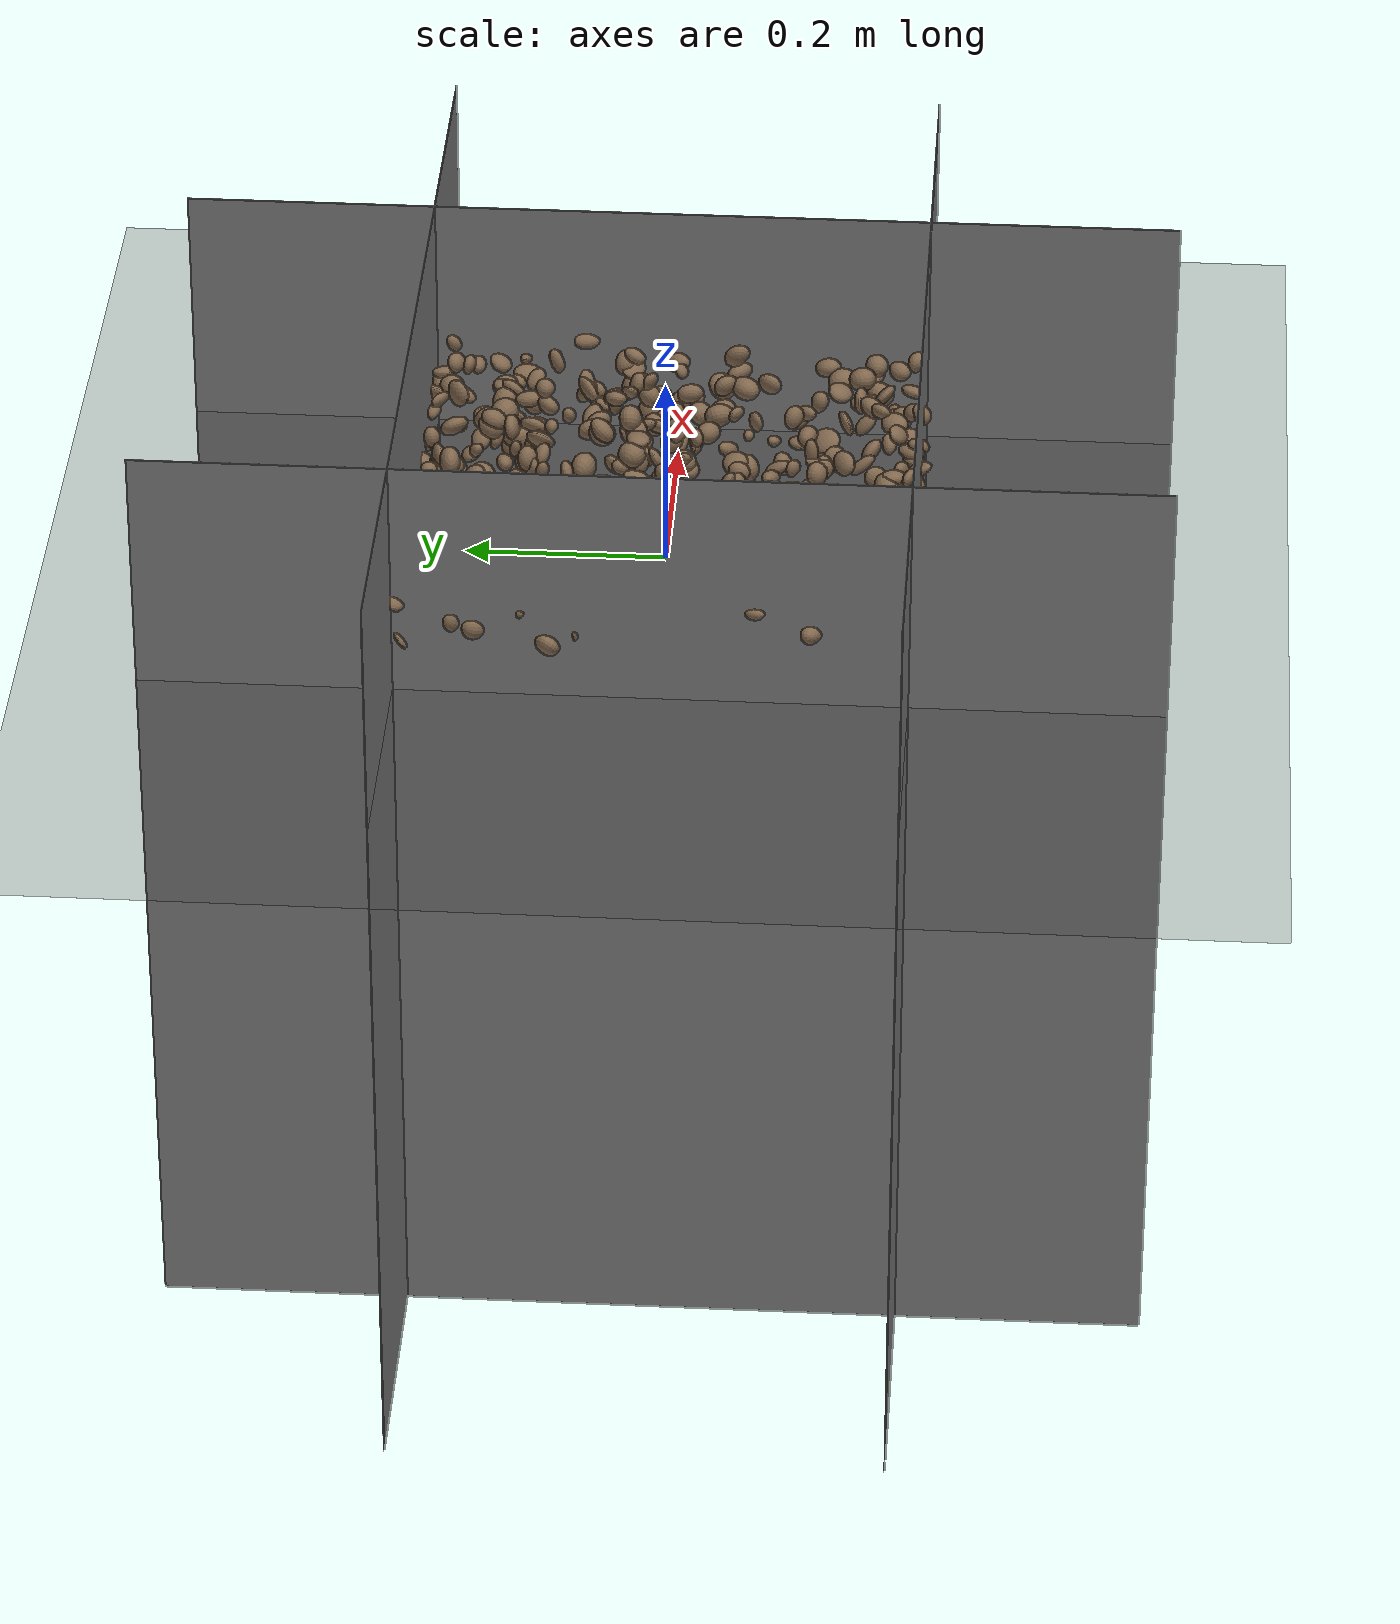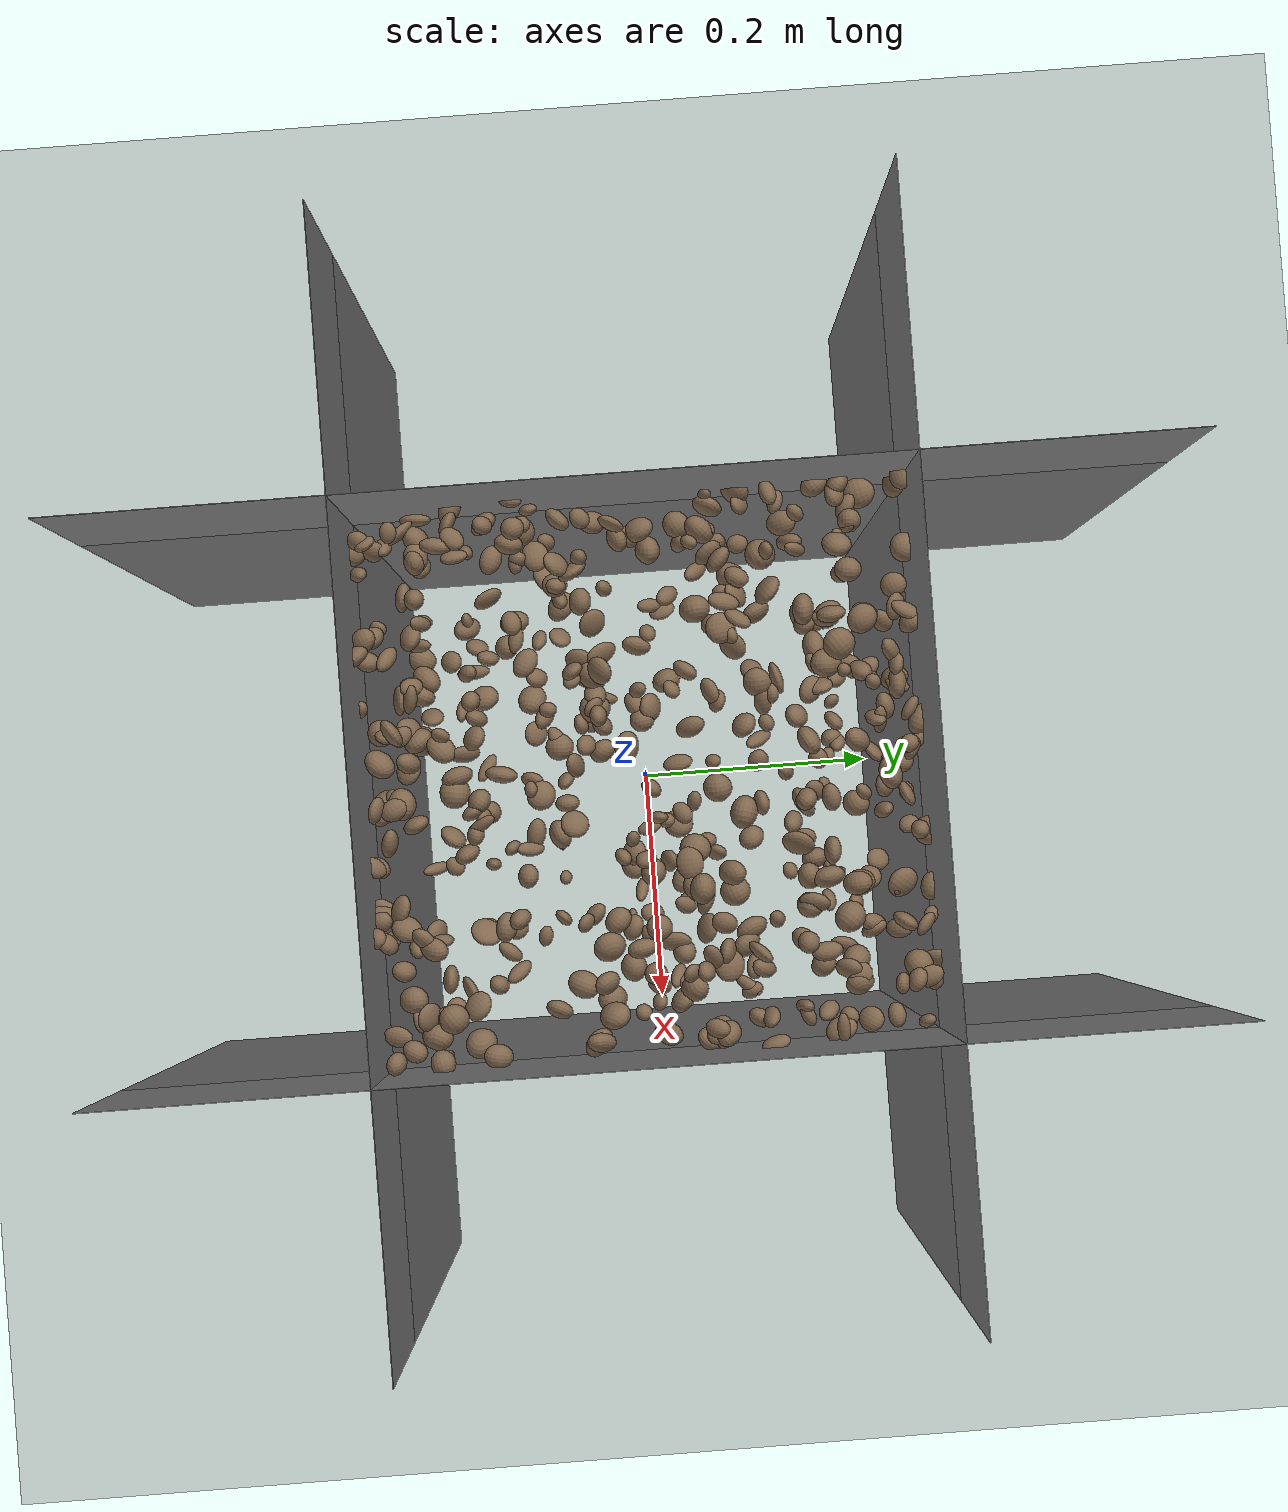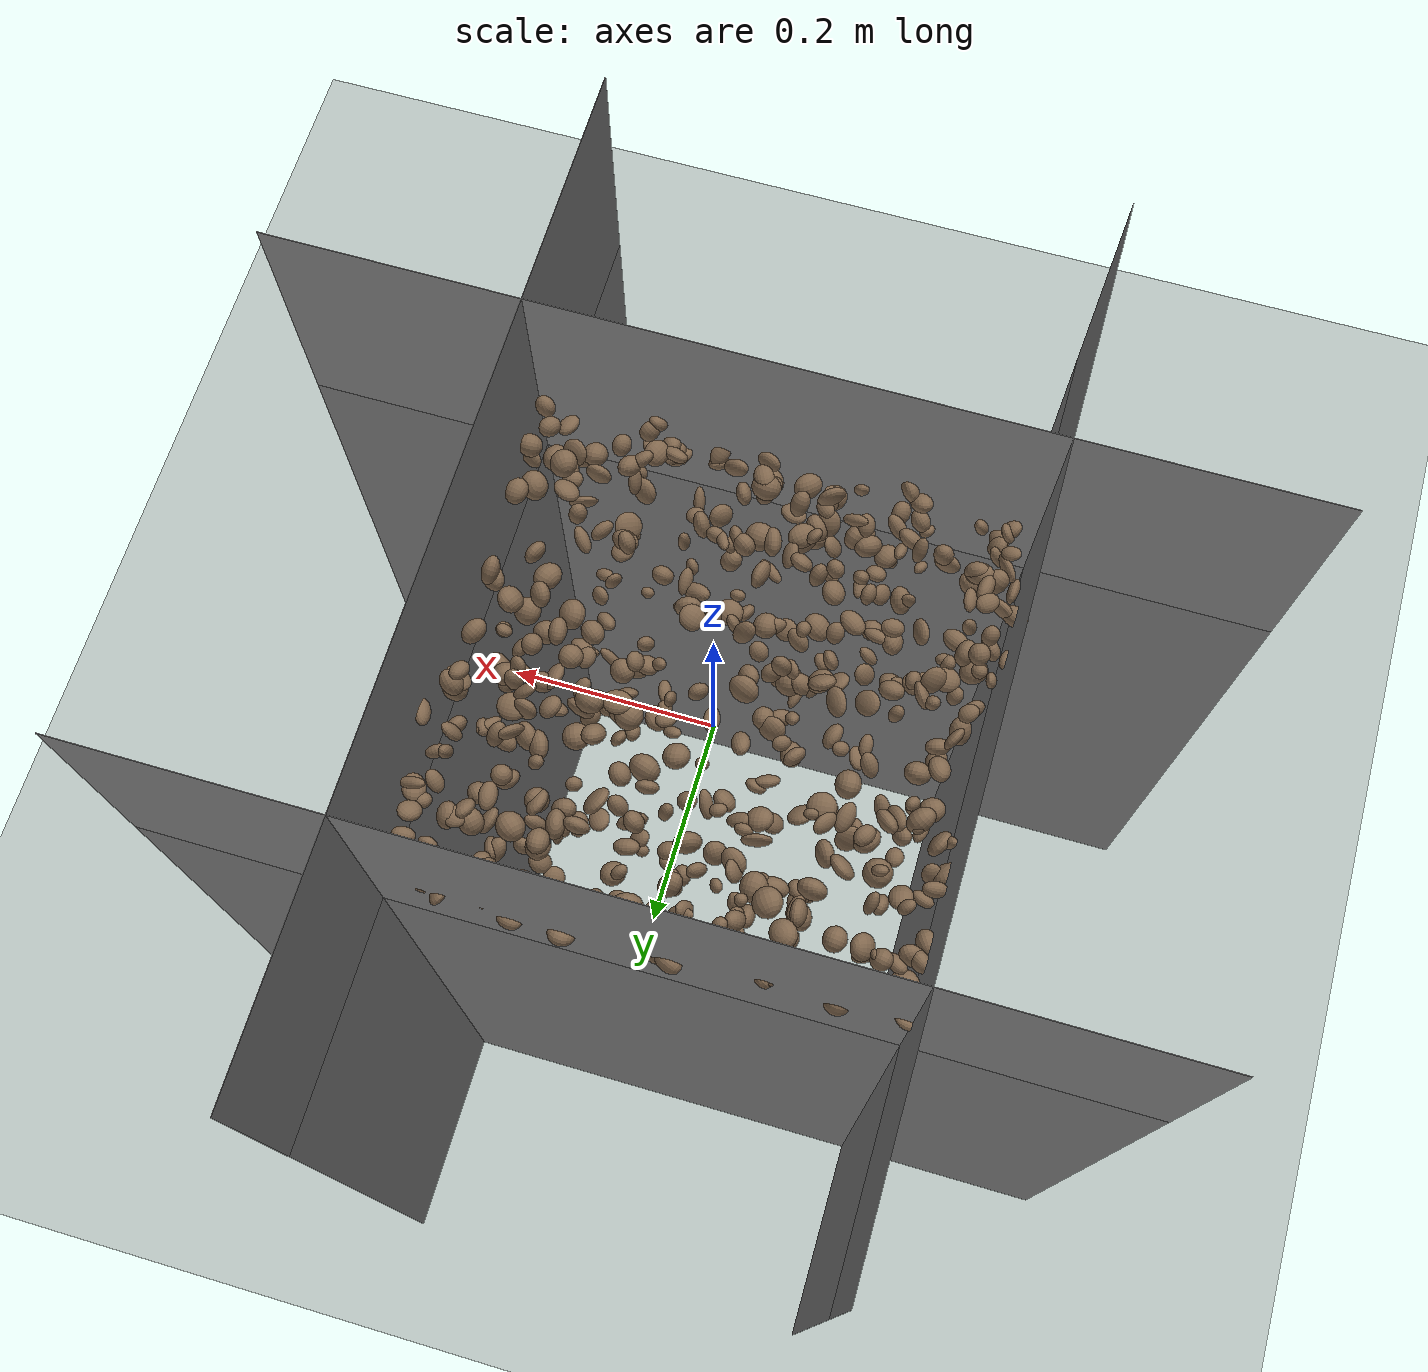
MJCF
<mujoco model="rocky_terrain_scene">

  <default>
    <default class="wall">
      <geom type="plane" size=".5 .5 .05" />
    </default>
  </default>

    <compiler angle="radian" inertiafromgeom="true" />
    <option timestep="0.002" gravity="0 0 -9.81" />

    <worldbody>

        <geom name="+x" class="wall" zaxis="1 0 0" pos="-.25 0 -.25" />
        <geom name="-x" class="wall" zaxis="-1 0 0" pos=".25 0 -.25" />
        <geom name="+y" class="wall" zaxis="0 1 0" pos="0 -.25 -.25" />
        <geom name="-y" class="wall" zaxis="0 -1 0" pos="0 .25 -.25" />

        <light name="sunlight" pos="5 5 5" dir="-1 -1 -1" diffuse="1 1 1" specular="0.5 0.5 0.5" ambient="0.5 0.5 0.5" />

        <geom name="ground_plane" type="plane" size="50 50 0.1" rgba="0.3 0.3 0.3 1" />

        <body name="rocky_terrain_body">

        </body>
    <body name="rock1" pos="0.20350912219481582 0.018304240437516384 0.06082536357927176"><joint type="free" /><geom type="ellipsoid" size="0.008488209986059406 0.013431796952947269 0.012827079204839359" quat="0.4295617621275138 0.2466941269164701 0.18265127097659167 0.1410928399794244" rgba="0.5 0.4 0.3 1" /></body><body name="rock2" pos="-0.0911934618068253 -0.04123348038952834 0.08062689347581822"><joint type="free" /><geom type="ellipsoid" size="0.013162320536673069 0.011973051526317996 0.008950524933142731" quat="0.6178411582296078 0.0589913319890176 0.20388271368867827 0.11928479609269634" rgba="0.5 0.4 0.3 1" /></body><body name="rock3" pos="0.22292955256228986 0.14696857267419677 0.06757115116750695"><joint type="free" /><geom type="ellipsoid" size="0.008212366826128633 0.006146750826555516 0.012120197523640538" quat="0.4243999733650203 0.2319396806310743 0.05893662436004592 0.2847237216438595" rgba="0.5 0.4 0.3 1" /></body><body name="rock4" pos="-0.08517616400141759 0.18748264933050957 0.056563368309271965"><joint type="free" /><geom type="ellipsoid" size="0.010710185063513837 0.013064357366107789 0.007842319639312137" quat="0.3440409163227259 0.13726230171621312 0.35104429187418396 0.167652490086877" rgba="0.5 0.4 0.3 1" /></body><body name="rock5" pos="-0.17304865619381876 -0.06709454921193558 0.07824234422264813"><joint type="free" /><geom type="ellipsoid" size="0.007200949018174217 0.009032388854285459 0.008634895547377702" quat="0.050801063874038474 0.07073520590262315 0.10075175028904525 0.7777119799342931" rgba="0.5 0.4 0.3 1" /></body><body name="rock6" pos="0.11210694296161233 0.03220144269569536 0.06072582097628863"><joint type="free" /><geom type="ellipsoid" size="0.009630441414616418 0.013295449080154738 0.005538391539691128" quat="0.08625424562649558 0.35306993419499094 0.19417872012782203 0.3664971000506914" rgba="0.5 0.4 0.3 1" /></body><body name="rock7" pos="0.02090689193178724 0.15824018970099368 0.0691347814821017"><joint type="free" /><geom type="ellipsoid" size="0.006341273688260557 0.005163469792644848 0.005984137729406485" quat="0.5671730802577221 0.08642122197138032 0.2571916875479698 0.08921401022292787" rgba="0.5 0.4 0.3 1" /></body><body name="rock8" pos="-0.16961173574281735 -0.19304589222228913 0.09149557246496963"><joint type="free" /><geom type="ellipsoid" size="0.008930452898224415 0.009654833295923431 0.01264084418832461" quat="0.4852009063445637 0.01398659730716039 0.06010571375902938 0.4407067825892465" rgba="0.5 0.4 0.3 1" /></body><body name="rock9" pos="0.15894656058447237 -0.2275831359991235 0.07702003661721493"><joint type="free" /><geom type="ellipsoid" size="0.011139222162384638 0.009155904541286251 0.009531405687963582" quat="0.446586184644072 0.02080739586196242 0.20548326800409838 0.3271231514898672" rgba="0.5 0.4 0.3 1" /></body><body name="rock10" pos="-0.07866867142790995 -0.13833367827467102 0.06614455657050802"><joint type="free" /><geom type="ellipsoid" size="0.009468541506970799 0.012878143882401806 0.012144408142342994" quat="0.6026658376126091 0.03962853041115177 0.2875726817031549 0.07013295027308435" rgba="0.5 0.4 0.3 1" /></body><body name="rock11" pos="0.16558150375312186 0.08966489783846698 0.09253513076762149"><joint type="free" /><geom type="ellipsoid" size="0.014277274073342897 0.0100717506213883 0.005601141028954992" quat="0.3298401025595651 0.37587718802990616 0.019270461848123942 0.27501224756240483" rgba="0.5 0.4 0.3 1" /></body><body name="rock12" pos="-0.015975527451864147 -0.14020135790440608 0.07251484910929334"><joint type="free" /><geom type="ellipsoid" size="0.0053208400937601345 0.006344878903103379 0.01387468813737677" quat="0.47897022520883636 0.20117747993118162 0.31188443194193394 0.00796786291804815" rgba="0.5 0.4 0.3 1" /></body><body name="rock13" pos="-0.07813044071502545 0.18258286090645348 0.08932361214475018"><joint type="free" /><geom type="ellipsoid" size="0.0062926101537603175 0.006953259351199588 0.006021131590262245" quat="0.3788056459591965 0.42286545090081695 0.07512438897575827 0.12320451416422826" rgba="0.5 0.4 0.3 1" /></body><body name="rock14" pos="-0.19757822051671853 -0.2423854791309829 0.07065118642492425"><joint type="free" /><geom type="ellipsoid" size="0.007404078360060574 0.006279870172352281 0.013430921150516952" quat="0.3015490668611264 0.006079484625359032 0.13043314740723702 0.5619383011062775" rgba="0.5 0.4 0.3 1" /></body><body name="rock15" pos="-0.07371951942885197 -0.09559291153769306 0.07459534668775053"><joint type="free" /><geom type="ellipsoid" size="0.0123414669898817 0.010324536907700538 0.014379825341862391" quat="0.3541377817044302 0.2131673706207398 0.10793566471727321 0.3247591829575567" rgba="0.5 0.4 0.3 1" /></body><body name="rock16" pos="0.03348293448176476 0.1403501851041149 0.09006774696649614"><joint type="free" /><geom type="ellipsoid" size="0.009193956122482111 0.013038861108833795 0.010231688548542364" quat="0.31909844018112976 0.36223113613803265 0.20507769640794765 0.11359272727288985" rgba="0.5 0.4 0.3 1" /></body><body name="rock17" pos="-0.029039788716582027 -0.07391977101344643 0.09691930873959807"><joint type="free" /><geom type="ellipsoid" size="0.012589014968097504 0.010743272135104603 0.01174637808443538" quat="0.2233289104630532 0.2882359125931452 0.24747726070343365 0.2409579162403679" rgba="0.5 0.4 0.3 1" /></body><body name="rock18" pos="-0.13578385204506271 0.15127873065741188 0.07316001291252375"><joint type="free" /><geom type="ellipsoid" size="0.009656095269556284 0.014452889380571585 0.01400510473467869" quat="0.17460752973011862 0.3400264571597885 0.3160748944459877 0.16929111866410526" rgba="0.5 0.4 0.3 1" /></body><body name="rock19" pos="-0.13978803819104846 -0.23413230268284108 0.06806939130390434"><joint type="free" /><geom type="ellipsoid" size="0.008995120240996357 0.010150015751504354 0.0116920657657855" quat="0.50056019894131 0.21523606283094926 0.1723029592597991 0.11190077896794165" rgba="0.5 0.4 0.3 1" /></body><body name="rock20" pos="0.12006518773848329 -0.12033918705392671 0.09520385864383578"><joint type="free" /><geom type="ellipsoid" size="0.009869958644266232 0.012032085112645176 0.008167441534411984" quat="0.09770028457990843 0.26487076371652674 0.3012877384695449 0.3361412132340199" rgba="0.5 0.4 0.3 1" /></body><body name="rock21" pos="0.03368516245673292 0.16293296827863202 0.08462692041192266"><joint type="free" /><geom type="ellipsoid" size="0.008802709561356162 0.007885430490592262 0.012530996533868341" quat="0.10394575579533273 0.4023551434440268 0.18242103026599252 0.31127807049464806" rgba="0.5 0.4 0.3 1" /></body><body name="rock22" pos="-0.006904326967961727 0.061144968646096365 0.0629101599557442"><joint type="free" /><geom type="ellipsoid" size="0.007438410619268355 0.006166356047829011 0.006382823261789762" quat="0.19422443955299476 0.3288990147425639 0.10170102367717375 0.3751755220272675" rgba="0.5 0.4 0.3 1" /></body><body name="rock23" pos="-0.23300283324783816 0.13347872951670925 0.07632605895591926"><joint type="free" /><geom type="ellipsoid" size="0.006207586262416056 0.008134821758274428 0.011051585475928247" quat="0.37957411100729027 0.2039721286507516 0.26883459428879486 0.1476191660531632" rgba="0.5 0.4 0.3 1" /></body><body name="rock24" pos="-0.004267069691499592 0.10114813373906834 0.0678400032494464"><joint type="free" /><geom type="ellipsoid" size="0.009106464454932246 0.007599513695658498 0.011373399494942427" quat="0.1808674002922802 0.35533521539266216 0.3627028601627859 0.10109452415227167" rgba="0.5 0.4 0.3 1" /></body><body name="rock25" pos="-0.2441957764030872 0.07119647426644665 0.06245417892411323"><joint type="free" /><geom type="ellipsoid" size="0.006095643296334735 0.012961391727161212 0.00580322841124602" quat="0.4507819698387745 0.35733150331484836 0.03995615462233615 0.15193037222404096" rgba="0.5 0.4 0.3 1" /></body><body name="rock26" pos="0.127646269238125 -0.19805712544608606 0.053703861311490464"><joint type="free" /><geom type="ellipsoid" size="0.0138552516121919 0.007340481825020475 0.011828659701600436" quat="0.26985499619565784 0.14692098380777216 0.4977011935193982 0.08552282647717181" rgba="0.5 0.4 0.3 1" /></body><body name="rock27" pos="0.06452028479337846 -0.24870215037319016 0.07396872660419314"><joint type="free" /><geom type="ellipsoid" size="0.014134811129244699 0.005615408643084674 0.008853894144207345" quat="0.3912775493979181 0.20115740590660283 0.2523839515443018 0.15518109315117729" rgba="0.5 0.4 0.3 1" /></body><body name="rock28" pos="-0.23622490381491856 -0.15911550184685364 0.08010412906519479"><joint type="free" /><geom type="ellipsoid" size="0.006008799742830056 0.01227835425526756 0.013368418197699919" quat="0.41388641820257227 0.19649714751729225 0.15669314436547152 0.23292328991466402" rgba="0.5 0.4 0.3 1" /></body><body name="rock29" pos="-0.2132982681915312 -0.10623113790463284 0.08038561322607984"><joint type="free" /><geom type="ellipsoid" size="0.00926130858014294 0.013092947471921215 0.012822444827209147" quat="0.06802421921010796 0.04704614384113901 0.27101168234650985 0.6139179546022433" rgba="0.5 0.4 0.3 1" /></body><body name="rock30" pos="0.09509564801765086 0.15771048550774514 0.06285070389388885"><joint type="free" /><geom type="ellipsoid" size="0.005655807998524515 0.01006533966319226 0.005354599182844004" quat="0.20511749496794573 0.15901306835337684 0.2708682034124746 0.3650012332662028" rgba="0.5 0.4 0.3 1" /></body><body name="rock31" pos="0.08646883359737811 0.14572138808290186 0.053017640786381576"><joint type="free" /><geom type="ellipsoid" size="0.011825140968319034 0.01257495176391362 0.009073428896735972" quat="0.22498781409673396 0.22316657013821442 0.25303020534819337 0.2988154104168583" rgba="0.5 0.4 0.3 1" /></body><body name="rock32" pos="-0.13761785487545403 0.10952831700826782 0.05095399447719499"><joint type="free" /><geom type="ellipsoid" size="0.013296603249028458 0.014048885531515863 0.008162143292043502" quat="0.11890928288117346 0.22992617007753707 0.2549266083467431 0.3962379386945464" rgba="0.5 0.4 0.3 1" /></body><body name="rock33" pos="0.13299336775046938 -0.23863480081189398 0.09777451370127768"><joint type="free" /><geom type="ellipsoid" size="0.007469604446803628 0.009241143767160738 0.011053180591993738" quat="0.007123311189018448 0.3437454758600301 0.37584080574385315 0.27329040720709824" rgba="0.5 0.4 0.3 1" /></body><body name="rock34" pos="-0.0363736326270801 0.11013605041666669 0.0951919371713488"><joint type="free" /><geom type="ellipsoid" size="0.0066750703625672175 0.006105933647346383 0.008228435579880863" quat="0.13088735226835235 0.28841823070506867 0.2876628355690207 0.29303158145755825" rgba="0.5 0.4 0.3 1" /></body><body name="rock35" pos="0.23113960965502356 0.003007918180469027 0.08757586032283168"><joint type="free" /><geom type="ellipsoid" size="0.009883934503585823 0.009976915271777126 0.013589448653146936" quat="0.06207758719453189 0.16945571909885018 0.445640035929578 0.3228266577770399" rgba="0.5 0.4 0.3 1" /></body><body name="rock36" pos="0.24071660733145905 0.1571299439550653 0.06281235104201917"><joint type="free" /><geom type="ellipsoid" size="0.01473804402516227 0.008085746646371905 0.011507941611818874" quat="0.21557063872451515 0.18244663193356564 0.24670951630980648 0.3552732130321127" rgba="0.5 0.4 0.3 1" /></body><body name="rock37" pos="-0.02297959547797218 0.10252523297054988 0.07751745696979445"><joint type="free" /><geom type="ellipsoid" size="0.014979651940280891 0.006943540624001734 0.005670961734588487" quat="0.24714781906067812 0.22041935167060467 0.48937786501740704 0.043054964251310196" rgba="0.5 0.4 0.3 1" /></body><body name="rock38" pos="-0.12936049680188727 -0.1932077581729304 0.07661770455655736"><joint type="free" /><geom type="ellipsoid" size="0.006125245826456726 0.013975688350108657 0.005535525941149841" quat="0.5492767878069311 0.18239394864338196 0.21257647677058808 0.05575278677909882" rgba="0.5 0.4 0.3 1" /></body><body name="rock39" pos="-0.14696646501239236 -0.1481660106956928 0.0665001703395718"><joint type="free" /><geom type="ellipsoid" size="0.00510199974605847 0.007750611449619553 0.012807630833788147" quat="0.07303085209465264 0.3934623407408705 0.42698949520869034 0.10651731195578654" rgba="0.5 0.4 0.3 1" /></body><body name="rock40" pos="-0.22079648797617246 -0.15551018548847256 0.09271918501554535"><joint type="free" /><geom type="ellipsoid" size="0.00949566952806908 0.006385044995231753 0.012030905676654855" quat="0.22804441083524596 0.09038240947487594 0.33713455262216485 0.34443862706771317" rgba="0.5 0.4 0.3 1" /></body><body name="rock41" pos="-0.13030263783957502 0.17372422112656927 0.056360557440521125"><joint type="free" /><geom type="ellipsoid" size="0.014445846687089321 0.014728881641897729 0.01081446321091565" quat="0.34579950727166947 0.021444322304453912 0.33990452685542405 0.2928516435684526" rgba="0.5 0.4 0.3 1" /></body><body name="rock42" pos="-0.12241448540597855 0.2022199498585262 0.0906966345147538"><joint type="free" /><geom type="ellipsoid" size="0.014073169558879859 0.012949031142831038 0.009784580491468828" quat="0.23594402813387705 0.07489070983414763 0.10310276902810903 0.5860624930038663" rgba="0.5 0.4 0.3 1" /></body><body name="rock43" pos="-0.1364388701567808 -0.24126496549879223 0.08945761020876486"><joint type="free" /><geom type="ellipsoid" size="0.013517985306545143 0.008563517922041396 0.01063196444308024" quat="0.10475878322801961 0.26594455532791494 0.2154842121649827 0.4138124492790828" rgba="0.5 0.4 0.3 1" /></body><body name="rock44" pos="-0.23156355491452424 -0.12814589602027426 0.08410423654706597"><joint type="free" /><geom type="ellipsoid" size="0.010340765791954554 0.007605770228806027 0.008598959313904963" quat="0.4356322454201922 0.020200987343739228 0.3244527022169403 0.21971406501912832" rgba="0.5 0.4 0.3 1" /></body><body name="rock45" pos="-0.052673247855850314 -0.2220442665099932 0.0925614344460608"><joint type="free" /><geom type="ellipsoid" size="0.01386743165180001 0.014787697684782358 0.0066900531857235785" quat="0.37721488670705783 0.3819773413048974 0.021643297267935763 0.21916447472010891" rgba="0.5 0.4 0.3 1" /></body><body name="rock46" pos="-0.16631262192652863 -0.02456072973379314 0.09242169313718568"><joint type="free" /><geom type="ellipsoid" size="0.006590802086882465 0.010952111519617034 0.0068080962148149085" quat="0.25292696927226216 0.2541682534853239 0.18598873684212433 0.3069160404002897" rgba="0.5 0.4 0.3 1" /></body><body name="rock47" pos="-0.0020488528409381424 0.15427571415708868 0.07907989953778816"><joint type="free" /><geom type="ellipsoid" size="0.008437950092303961 0.007314775149509236 0.010253114364120065" quat="0.13147932436790383 0.2971152420673752 0.34840746733243605 0.22299796623228488" rgba="0.5 0.4 0.3 1" /></body><body name="rock48" pos="-0.15159273601143503 -0.18740563619426676 0.06577788181527984"><joint type="free" /><geom type="ellipsoid" size="0.005072177791637876 0.009091591820051755 0.005746129698405521" quat="0.2511273558126927 0.14905805752175996 0.5094658128638918 0.09034877380165557" rgba="0.5 0.4 0.3 1" /></body><body name="rock49" pos="0.12745517106432241 -0.2481997237713232 0.09991379621785185"><joint type="free" /><geom type="ellipsoid" size="0.009321476773461398 0.007497728758103312 0.011369981210799473" quat="0.1330363441148788 0.04195030567190173 0.21243802244297164 0.6125753277702478" rgba="0.5 0.4 0.3 1" /></body><body name="rock50" pos="0.0698730949553431 -0.1403787095900058 0.08625154151254877"><joint type="free" /><geom type="ellipsoid" size="0.00672313537237087 0.014754208146407082 0.005478769408939125" quat="0.27682564916430413 0.2673183668338034 0.23784882579915836 0.21800715820273406" rgba="0.5 0.4 0.3 1" /></body><body name="rock51" pos="0.1068603234947621 0.19294021153086754 0.06549169278486042"><joint type="free" /><geom type="ellipsoid" size="0.010175771082009812 0.01224825027905034 0.007471541622863997" quat="0.16735611012404566 0.42720601170751527 0.29215071911043616 0.11328715905800303" rgba="0.5 0.4 0.3 1" /></body><body name="rock52" pos="0.16674094971402825 0.16589610563119567 0.05439699802278637"><joint type="free" /><geom type="ellipsoid" size="0.014435079614867515 0.011472966691594678 0.006446397977740062" quat="0.4446329355798213 0.13427368272929568 0.2537493489208376 0.16734403277004536" rgba="0.5 0.4 0.3 1" /></body><body name="rock53" pos="0.17788099826829018 0.08663573696599108 0.05395073227965311"><joint type="free" /><geom type="ellipsoid" size="0.008089324198900008 0.009295881339453867 0.013668163733934518" quat="0.20726662517416072 0.3298545035051053 0.00753005400446555 0.45534881731626836" rgba="0.5 0.4 0.3 1" /></body><body name="rock54" pos="0.18406636794036324 0.246302450882108 0.07158834149964821"><joint type="free" /><geom type="ellipsoid" size="0.014052822498007562 0.011440879801743235 0.005830483791734716" quat="0.29510956466800575 0.2185536769505254 0.09821815437201857 0.3881186040094504" rgba="0.5 0.4 0.3 1" /></body><body name="rock55" pos="0.17085753151258543 -0.02347481098288695 0.06513424011989723"><joint type="free" /><geom type="ellipsoid" size="0.011364493875071935 0.013710112850531624 0.01225601971421128" quat="0.353726005139104 0.03355945822874905 0.2316677672536181 0.3810467693785287" rgba="0.5 0.4 0.3 1" /></body><body name="rock56" pos="0.19581683057682053 -0.1833392505888743 0.0678787831858009"><joint type="free" /><geom type="ellipsoid" size="0.010242574518180815 0.007251256225464204 0.0093865032438199" quat="0.4601297300818891 0.4021926806396665 0.09690352102505345 0.040774068253391034" rgba="0.5 0.4 0.3 1" /></body><body name="rock57" pos="0.18192460648707093 0.14564833445406716 0.0630710032240735"><joint type="free" /><geom type="ellipsoid" size="0.010403705205744691 0.01311244064571149 0.010126889003847414" quat="0.3034529762198581 0.029489130098601792 0.38541256555150055 0.2816453281300395" rgba="0.5 0.4 0.3 1" /></body><body name="rock58" pos="0.013317215836462226 -0.14846518964566408 0.0960584197470566"><joint type="free" /><geom type="ellipsoid" size="0.01150661321359604 0.012494348217147958 0.009511330649098471" quat="0.08150880744938836 0.15756973339866817 0.40134216717504306 0.3595792919769005" rgba="0.5 0.4 0.3 1" /></body><body name="rock59" pos="-0.09200036807516193 -0.08973538232274442 0.08557793490821859"><joint type="free" /><geom type="ellipsoid" size="0.00670148004958414 0.010967947836265665 0.008684809763780766" quat="0.12466232382018934 0.3101954548209579 0.16511497234509845 0.40002724901375425" rgba="0.5 0.4 0.3 1" /></body><body name="rock60" pos="0.2126119668945619 -0.04336798385293017 0.07250831786067348"><joint type="free" /><geom type="ellipsoid" size="0.014799253544530253 0.010441752339803774 0.013158708750467568" quat="0.304466421155287 0.30009287104592436 0.032759018161503665 0.3626816896372851" rgba="0.5 0.4 0.3 1" /></body><body name="rock61" pos="0.12815297538486053 -0.0622735308929846 0.09190316238373378"><joint type="free" /><geom type="ellipsoid" size="0.009252066299910471 0.009002559944478686 0.005608382095910323" quat="0.0796456519795196 0.14321591548277474 0.28540581165628015 0.4917326208814256" rgba="0.5 0.4 0.3 1" /></body><body name="rock62" pos="-0.19645762015291185 0.19094164728536128 0.05067628370279123"><joint type="free" /><geom type="ellipsoid" size="0.006958802941501852 0.012763015038530463 0.006296885678989309" quat="0.30772016751590303 0.003869156755826809 0.16342295631307013 0.5249877194152" rgba="0.5 0.4 0.3 1" /></body><body name="rock63" pos="-0.23609623583582517 0.1866455423806082 0.07763690843623722"><joint type="free" /><geom type="ellipsoid" size="0.008229446949140313 0.014492584164536033 0.01070869841303165" quat="0.07173558534558411 0.32304504488651503 0.34879347940720135 0.25642589036069946" rgba="0.5 0.4 0.3 1" /></body><body name="rock64" pos="0.029801233160252016 -0.20672308960675878 0.08349056732753918"><joint type="free" /><geom type="ellipsoid" size="0.007236994327330833 0.012800292231576395 0.011160722964717037" quat="0.5801721272385962 0.21881753468363466 0.10082886644341359 0.10018147163435547" rgba="0.5 0.4 0.3 1" /></body><body name="rock65" pos="-0.14723570097051158 0.08094248241962065 0.0829738045372857"><joint type="free" /><geom type="ellipsoid" size="0.00645774031333771 0.014861720065863566 0.008716738728176368" quat="0.11203363684102771 0.3263342475972873 0.051127924936096046 0.5105041906255889" rgba="0.5 0.4 0.3 1" /></body><body name="rock66" pos="0.21238351425627494 -0.017638479467893597 0.05834996130820242"><joint type="free" /><geom type="ellipsoid" size="0.007554662582618472 0.0068668430369082665 0.008075383447041005" quat="0.4076072730140013 0.1120599282627113 0.19028961436304218 0.2900431843602453" rgba="0.5 0.4 0.3 1" /></body><body name="rock67" pos="0.19563558081677063 0.07779242630778632 0.05733112418109343"><joint type="free" /><geom type="ellipsoid" size="0.01369803675848975 0.006175905474457677 0.005108422188385284" quat="0.5362993142602228 0.16753608047745724 0.02632563939668612 0.2698389658656338" rgba="0.5 0.4 0.3 1" /></body><body name="rock68" pos="0.13169192871610313 -0.2370091299100121 0.06987488713582309"><joint type="free" /><geom type="ellipsoid" size="0.007897171350618442 0.005928972468685358 0.01002092302298472" quat="0.27658876247604974 0.2791802213675198 0.1129005490313851 0.3313304671250453" rgba="0.5 0.4 0.3 1" /></body><body name="rock69" pos="-0.21762452016425315 0.010227693022845541 0.07704455490851235"><joint type="free" /><geom type="ellipsoid" size="0.014069228118909562 0.01106467401473233 0.008867238668827148" quat="0.0034181664643429988 0.36536266332004663 0.42802994454125065 0.20318922567435974" rgba="0.5 0.4 0.3 1" /></body><body name="rock70" pos="0.1370648745463861 0.001880116407845911 0.08658308056892502"><joint type="free" /><geom type="ellipsoid" size="0.011539100706397052 0.010573696092456302 0.011571073415710955" quat="0.10546641760974984 0.061224794866303604 0.41082677716967453 0.422482010354272" rgba="0.5 0.4 0.3 1" /></body><body name="rock71" pos="0.05717748584070642 -0.015508341140450133 0.08159347779937427"><joint type="free" /><geom type="ellipsoid" size="0.00617417811921917 0.008929303890491654 0.0052684433819338" quat="0.3255684429032981 0.08015922797774094 0.24414002993418676 0.3501322991847741" rgba="0.5 0.4 0.3 1" /></body><body name="rock72" pos="-0.11549655706514916 0.0005045862961842729 0.06059580533555124"><joint type="free" /><geom type="ellipsoid" size="0.01301702290822843 0.00768920856849416 0.00991232494327893" quat="0.1469681379612807 0.466476513279611 0.3638066699167196 0.022748678842388723" rgba="0.5 0.4 0.3 1" /></body><body name="rock73" pos="-0.20568137063583092 -0.1906061829693917 0.07766822362161506"><joint type="free" /><geom type="ellipsoid" size="0.010175092783214542 0.013395032188203863 0.01407455817167785" quat="0.4238234968651389 0.046756846556077564 0.08874304741772167 0.4406766091610619" rgba="0.5 0.4 0.3 1" /></body><body name="rock74" pos="0.06946983495808956 0.13664103122415666 0.05443692442500231"><joint type="free" /><geom type="ellipsoid" size="0.010320711867318831 0.0055360119748299255 0.012189510994669667" quat="0.3336256659182702 0.4098529728924948 0.21087095194929045 0.04565040923994457" rgba="0.5 0.4 0.3 1" /></body><body name="rock75" pos="-0.18372678119445635 0.2448004209092008 0.07910774650452186"><joint type="free" /><geom type="ellipsoid" size="0.013125964551612076 0.011672395921056174 0.013035205118865148" quat="0.03592216078806281 0.012822461904082982 0.6636609432547006 0.28759443405315366" rgba="0.5 0.4 0.3 1" /></body><body name="rock76" pos="0.14493712446162654 0.2438559470106899 0.07314997667167225"><joint type="free" /><geom type="ellipsoid" size="0.0062721944785561 0.00573256544653996 0.009358807053309257" quat="0.3404724183546621 0.23747172635302144 0.11514176099220404 0.30691409430011246" rgba="0.5 0.4 0.3 1" /></body><body name="rock77" pos="-0.15274658822134446 0.2350633237921836 0.054744485136257376"><joint type="free" /><geom type="ellipsoid" size="0.011886910293531693 0.00768603923434967 0.01119335051012833" quat="0.147589068283809 0.25936522155944775 0.2912460527841024 0.3017996573726408" rgba="0.5 0.4 0.3 1" /></body><body name="rock78" pos="-0.13122764008172766 0.2329554812677055 0.08415357340697854"><joint type="free" /><geom type="ellipsoid" size="0.010015948947462805 0.005944314314928776 0.012590603153697545" quat="0.2989331527027046 0.20829956456406515 0.3907800064354551 0.10198727629777525" rgba="0.5 0.4 0.3 1" /></body><body name="rock79" pos="0.10022372627300252 0.15914011263332167 0.061182403813520005"><joint type="free" /><geom type="ellipsoid" size="0.012132374050398471 0.01327778388949618 0.005148880763903562" quat="0.3695598092539401 0.10413749627127693 0.4020429660242529 0.12425972845053014" rgba="0.5 0.4 0.3 1" /></body><body name="rock80" pos="0.11400083253293297 -0.24575504588635622 0.06987480975541646"><joint type="free" /><geom type="ellipsoid" size="0.009444068172677515 0.008050158822587646 0.011826349671184792" quat="0.3022374855600216 0.4653212776062941 0.22056831324011086 0.011872923593573429" rgba="0.5 0.4 0.3 1" /></body><body name="rock81" pos="-0.23051185138280184 -0.21164236712434298 0.09211549344856097"><joint type="free" /><geom type="ellipsoid" size="0.007554683107471571 0.009962088880072259 0.005044690281080059" quat="0.45054949422965085 0.0878772397154945 0.058028611802309955 0.4035446542525447" rgba="0.5 0.4 0.3 1" /></body><body name="rock82" pos="-0.13594427199172898 -0.1984813136351975 0.09498535401274102"><joint type="free" /><geom type="ellipsoid" size="0.007825293373240012 0.011454002262011306 0.013525737929355502" quat="0.48867753871308367 0.08401445359309126 0.21306260526325582 0.21424540243056928" rgba="0.5 0.4 0.3 1" /></body><body name="rock83" pos="-0.19626143605190743 -0.10191344061816959 0.06264885217821539"><joint type="free" /><geom type="ellipsoid" size="0.0060330165369715085 0.006118584646554693 0.008414034717391446" quat="0.11176846992541585 0.41019532143982124 0.14683840596679845 0.33119780266796456" rgba="0.5 0.4 0.3 1" /></body><body name="rock84" pos="-0.23569983211048812 0.07333041389259987 0.05842513482562595"><joint type="free" /><geom type="ellipsoid" size="0.013838627183852484 0.01341944738864266 0.0073848466399963385" quat="0.43291179493008464 0.20081318550182764 0.2582390806686457 0.10803593889944207" rgba="0.5 0.4 0.3 1" /></body><body name="rock85" pos="-0.015780287001214588 0.24683458392498814 0.06523242803987017"><joint type="free" /><geom type="ellipsoid" size="0.011768161950677695 0.0061218996626295225 0.00840680396740353" quat="0.17849011094490538 0.08751997790148275 0.6826554747668147 0.05133443638679721" rgba="0.5 0.4 0.3 1" /></body><body name="rock86" pos="0.04616888219541854 0.025986186084097473 0.0544043354340801"><joint type="free" /><geom type="ellipsoid" size="0.012568597940353716 0.009281625165873098 0.013481477633073828" quat="0.20247398951245027 0.0729464280947495 0.3089019869285378 0.4156775954642624" rgba="0.5 0.4 0.3 1" /></body><body name="rock87" pos="-0.22126103168658634 0.044480128376550965 0.059847166525688694"><joint type="free" /><geom type="ellipsoid" size="0.012001266102242003 0.011216153324231858 0.01246314833631076" quat="0.09045466006770946 0.2848213141738245 0.2938004460880896 0.3309235796703765" rgba="0.5 0.4 0.3 1" /></body><body name="rock88" pos="-0.21388972555438984 0.1375385757090568 0.07693327476725932"><joint type="free" /><geom type="ellipsoid" size="0.013782137052422434 0.008056035468194705 0.011382249585024352" quat="0.13906065635650788 0.3177902489088668 0.23897316144272773 0.3041759332918977" rgba="0.5 0.4 0.3 1" /></body><body name="rock89" pos="0.16976852921843089 0.14934976621435797 0.07607366741548965"><joint type="free" /><geom type="ellipsoid" size="0.014166839004554323 0.008838042376436709 0.007714651635746498" quat="0.06305561277010055 0.4320074053097543 0.48196785673617104 0.022969125183974155" rgba="0.5 0.4 0.3 1" /></body><body name="rock90" pos="-0.20471273155369307 0.04615459353590451 0.05600562636481611"><joint type="free" /><geom type="ellipsoid" size="0.007025273181503639 0.012256405834086253 0.007515925221026549" quat="0.3208157765049784 0.18110367672614125 0.2698529838133843 0.22822756295549615" rgba="0.5 0.4 0.3 1" /></body><body name="rock91" pos="0.12975260280080003 0.17937640009792555 0.05152575765841106"><joint type="free" /><geom type="ellipsoid" size="0.009935023217224843 0.0062763491226712695 0.00920032260933475" quat="0.3620644400171871 0.08751828118116387 0.48971212278517295 0.060705156016476074" rgba="0.5 0.4 0.3 1" /></body><body name="rock92" pos="-0.07303659372242083 0.028658000879801748 0.08315425424711459"><joint type="free" /><geom type="ellipsoid" size="0.007566356093292291 0.005806816133561822 0.008867200948518499" quat="0.3419016022204705 0.038814556375478426 0.3617387177470837 0.2575451236569674" rgba="0.5 0.4 0.3 1" /></body><body name="rock93" pos="-0.0653766017493354 -0.18608327515513678 0.06308176094170617"><joint type="free" /><geom type="ellipsoid" size="0.01005411962840818 0.005340452868171889 0.013433676611678276" quat="0.364719822165893 0.07944611508089787 0.14383952243734524 0.41199454031586386" rgba="0.5 0.4 0.3 1" /></body><body name="rock94" pos="0.10195633868084852 0.1391495389923762 0.06452985029035833"><joint type="free" /><geom type="ellipsoid" size="0.010428494827097727 0.014107360623091893 0.010708922524411114" quat="0.2979592092945877 0.14616033582217802 0.1996416324315056 0.35623882245172867" rgba="0.5 0.4 0.3 1" /></body><body name="rock95" pos="0.12792379280894045 0.13785291471304245 0.0655117448100401"><joint type="free" /><geom type="ellipsoid" size="0.012035214592125067 0.01376757381980305 0.011451260061253564" quat="0.305375498918525 0.2918246122858421 0.21950686058110705 0.18329302821452587" rgba="0.5 0.4 0.3 1" /></body><body name="rock96" pos="0.03963013099031193 -0.06518294821439324 0.08908950265829318"><joint type="free" /><geom type="ellipsoid" size="0.005877945260650529 0.007701093716310524 0.006195648863370349" quat="0.016202041899327422 0.20894814927689376 0.6319538976117023 0.14289591121207665" rgba="0.5 0.4 0.3 1" /></body><body name="rock97" pos="0.22997053455889438 -0.22237012664457406 0.08675483846826128"><joint type="free" /><geom type="ellipsoid" size="0.01161863167834724 0.009455427710424971 0.009574654018506403" quat="0.2801930086403807 0.3584480982923427 0.15071352332067234 0.21064536974660425" rgba="0.5 0.4 0.3 1" /></body><body name="rock98" pos="0.07877279289292316 0.015130189556221751 0.06736263109754086"><joint type="free" /><geom type="ellipsoid" size="0.005491915705816935 0.012715445136084795 0.009683178424915562" quat="0.29518481950380615 0.12015320036953793 0.3199163951923507 0.2647455849343051" rgba="0.5 0.4 0.3 1" /></body><body name="rock99" pos="0.08639086254576628 -0.07715660781702743 0.09319273638611764"><joint type="free" /><geom type="ellipsoid" size="0.005217439978474193 0.0053849432640697935 0.006199854886510492" quat="0.25646305896607297 0.25461321860940384 0.21984762183551998 0.2690761005890033" rgba="0.5 0.4 0.3 1" /></body><body name="rock100" pos="0.11032704148060002 0.07165751939240916 0.07473514996007725"><joint type="free" /><geom type="ellipsoid" size="0.012036131796554227 0.013742116040733908 0.013256633960678495" quat="0.3580778768344158 0.025028238101645527 0.43544845906170593 0.18144542600223273" rgba="0.5 0.4 0.3 1" /></body><body name="rock101" pos="-0.19551368991806295 -0.04484169448199793 0.09109490459877372"><joint type="free" /><geom type="ellipsoid" size="0.007379851817509045 0.010352727887265337 0.006711792720956483" quat="0.4518102661265857 0.3319495878498437 0.07274163414470833 0.14349851187886237" rgba="0.5 0.4 0.3 1" /></body><body name="rock102" pos="0.1536780697179732 0.21375723816809516 0.0890000135672766"><joint type="free" /><geom type="ellipsoid" size="0.013122899609381875 0.006299086616096881 0.008756064936645165" quat="0.19403426821272882 0.31853479813756796 0.16550922492677173 0.3219217087229314" rgba="0.5 0.4 0.3 1" /></body><body name="rock103" pos="-0.01958043111549901 -0.2113053081179037 0.06056249022670839"><joint type="free" /><geom type="ellipsoid" size="0.011407087936528896 0.006095532643369845 0.013209716205799957" quat="0.2568174141857231 0.3535766626049291 0.13870615468185388 0.25089976852749396" rgba="0.5 0.4 0.3 1" /></body><body name="rock104" pos="-0.22040611032647867 -0.21842797508851802 0.06629164401969441"><joint type="free" /><geom type="ellipsoid" size="0.007648165184314437 0.014280795060266766 0.006302283746684597" quat="0.1952598721862182 0.33737915187557543 0.3016151286253793 0.165745847312827" rgba="0.5 0.4 0.3 1" /></body><body name="rock105" pos="-0.14840536205634625 -0.22922395626534114 0.06012139968676544"><joint type="free" /><geom type="ellipsoid" size="0.008270944354975149 0.005411325043213392 0.007750777758643447" quat="0.03851749276809917 0.39351267245666205 0.2830524197069622 0.2849174150682767" rgba="0.5 0.4 0.3 1" /></body><body name="rock106" pos="-0.07363245433047572 -0.03965145880410825 0.0650397792492979"><joint type="free" /><geom type="ellipsoid" size="0.00986969681811102 0.013363549193603115 0.008829937013221432" quat="0.16854800898301436 0.35733796809547047 0.3450762920080893 0.1290377309134259" rgba="0.5 0.4 0.3 1" /></body><body name="rock107" pos="-0.18849347056465748 0.11721431902215462 0.06248297206788997"><joint type="free" /><geom type="ellipsoid" size="0.013887560714455793 0.014676565055753883 0.01345030996812295" quat="0.3420111687045129 0.465500570902664 0.13198751221110236 0.06050074818172066" rgba="0.5 0.4 0.3 1" /></body><body name="rock108" pos="0.16867927091265372 -0.18581792146075055 0.08776893179996462"><joint type="free" /><geom type="ellipsoid" size="0.006856937473942187 0.012905125871666107 0.013475403902373555" quat="0.5080571692026118 0.004849606238811263 0.03734856551416862 0.4497446590444084" rgba="0.5 0.4 0.3 1" /></body><body name="rock109" pos="-0.14221521480796245 -0.10865574134392325 0.08797757307691799"><joint type="free" /><geom type="ellipsoid" size="0.008744296891344608 0.011346498946002436 0.007346590935755797" quat="0.06462240640783638 0.4116710940302023 0.4953797648311259 0.02832673473083542" rgba="0.5 0.4 0.3 1" /></body><body name="rock110" pos="-0.1026692470265616 0.15844197503213542 0.06985238090268533"><joint type="free" /><geom type="ellipsoid" size="0.009821167470303841 0.014180081782023169 0.011016558657241255" quat="0.11565374048795937 0.4184100142192853 0.4324850413032452 0.03345120398951019" rgba="0.5 0.4 0.3 1" /></body><body name="rock111" pos="-0.19141670566361207 0.06997667158431065 0.08650408308050478"><joint type="free" /><geom type="ellipsoid" size="0.006282488802426938 0.009894446453160406 0.014006083261983722" quat="0.2540458411556477 0.5143482972616774 0.026531116918790537 0.2050747446638844" rgba="0.5 0.4 0.3 1" /></body><body name="rock112" pos="-0.22426203851632365 0.19586195181817645 0.0732929156431475"><joint type="free" /><geom type="ellipsoid" size="0.007069182400172465 0.00858348293893661 0.012470987368422927" quat="0.32676558937672406 0.2943367259788864 0.3123782031102717 0.06651948153411798" rgba="0.5 0.4 0.3 1" /></body><body name="rock113" pos="-0.10651326454738791 -0.05187158110685164 0.0634896539199258"><joint type="free" /><geom type="ellipsoid" size="0.00589907378314168 0.012755457142033267 0.011132154529237086" quat="0.2796744571725951 0.03839108471171108 0.5213339888669581 0.1606004692487356" rgba="0.5 0.4 0.3 1" /></body><body name="rock114" pos="-0.08116893585117557 -0.20283791363395376 0.09538383409930423"><joint type="free" /><geom type="ellipsoid" size="0.005963730838968847 0.01430705233728767 0.006943233283071856" quat="0.39778852307725004 0.031547615053247276 0.2062928534820529 0.36437100838744985" rgba="0.5 0.4 0.3 1" /></body><body name="rock115" pos="-0.2252694119842636 -0.09442991321265787 0.07054068191911614"><joint type="free" /><geom type="ellipsoid" size="0.012042360783429455 0.013873102001019644 0.010514137533320282" quat="0.3333916496138427 0.06542697882254547 0.12486104879457299 0.47632032276903874" rgba="0.5 0.4 0.3 1" /></body><body name="rock116" pos="-0.028962086715986324 -0.05053741891511171 0.0887748257211059"><joint type="free" /><geom type="ellipsoid" size="0.008954662795757967 0.00679510417764643 0.010141166547194283" quat="0.5038326056299608 0.2043909870545673 0.15678541402958052 0.13499099328589145" rgba="0.5 0.4 0.3 1" /></body><body name="rock117" pos="0.04270457518463883 -0.15429241290280205 0.08929123385151065"><joint type="free" /><geom type="ellipsoid" size="0.009409204130467082 0.007446099221087778 0.009679768370337717" quat="0.10556418258507021 0.5600008722004912 0.0007530304517416038 0.33368191476269704" rgba="0.5 0.4 0.3 1" /></body><body name="rock118" pos="0.1408662814516658 -0.19816243979625353 0.09680592418788214"><joint type="free" /><geom type="ellipsoid" size="0.009443841144434157 0.013741355319889532 0.01066895150887531" quat="0.2888860831154235 0.16529890315112333 0.47772092045553327 0.06809409327791989" rgba="0.5 0.4 0.3 1" /></body><body name="rock119" pos="-0.09839827166056925 -0.18795955634335765 0.07939847377074158"><joint type="free" /><geom type="ellipsoid" size="0.01055460762885407 0.011704855535364593 0.01453275841534157" quat="0.24981968569308025 0.07163222170564254 0.2671256923742581 0.41142240022701904" rgba="0.5 0.4 0.3 1" /></body><body name="rock120" pos="-0.07692739311715685 0.19063604009778717 0.07018085416289181"><joint type="free" /><geom type="ellipsoid" size="0.005467372661842057 0.008629950597511036 0.006484337863620985" quat="0.12019591110728306 0.22007325856282323 0.3671970170866249 0.2925338132432688" rgba="0.5 0.4 0.3 1" /></body><body name="rock121" pos="0.2000707488498465 0.24265536269178933 0.07309986449684003"><joint type="free" /><geom type="ellipsoid" size="0.011550883819227503 0.008534842270032646 0.011602423718905299" quat="0.7810439649596023 0.035598656384652747 0.17338271821047024 0.009974660445274765" rgba="0.5 0.4 0.3 1" /></body><body name="rock122" pos="0.03987101591535458 -0.0659626992202127 0.08962975708300998"><joint type="free" /><geom type="ellipsoid" size="0.012770919492072924 0.007043922238603735 0.012807347281814898" quat="0.35885914919003375 0.19764868860468016 0.19251507339855567 0.2509770888067305" rgba="0.5 0.4 0.3 1" /></body><body name="rock123" pos="0.13966302260400504 -0.21564555029476679 0.055527597575743826"><joint type="free" /><geom type="ellipsoid" size="0.007286448695333518 0.007218167101794522 0.010638377909967342" quat="0.42042793270644024 0.0958350260209665 0.1962525525615726 0.28748448871102067" rgba="0.5 0.4 0.3 1" /></body><body name="rock124" pos="-0.0399085257208317 0.23827721148579312 0.08814020440601744"><joint type="free" /><geom type="ellipsoid" size="0.012107759312238012 0.005579106651258058 0.00662388092673369" quat="0.20593939070574313 0.09034069969155822 0.0023677026693532284 0.7013522069333453" rgba="0.5 0.4 0.3 1" /></body><body name="rock125" pos="-0.22548097480343282 -0.23891140851896048 0.08662746883974089"><joint type="free" /><geom type="ellipsoid" size="0.009715592623972612 0.010378139343075948 0.007253884895461043" quat="0.2594781019988928 0.22985856225724355 0.03868960805551115 0.4719737276883525" rgba="0.5 0.4 0.3 1" /></body><body name="rock126" pos="-0.037912665361565734 -0.178274303010724 0.0692615827779616"><joint type="free" /><geom type="ellipsoid" size="0.014486224816893049 0.007940240450818785 0.008994501495986806" quat="0.5975183193955946 0.05759076784732022 0.12685098011507692 0.21803993264200827" rgba="0.5 0.4 0.3 1" /></body><body name="rock127" pos="-0.12969493989603725 0.1759532579123328 0.07502411656566028"><joint type="free" /><geom type="ellipsoid" size="0.013310577585894778 0.012105600557391393 0.007341341157704649" quat="0.17257864938811446 0.3061027493664009 0.26674549890459703 0.2545731023408876" rgba="0.5 0.4 0.3 1" /></body><body name="rock128" pos="-0.026538311267722214 -0.23569302125331554 0.07532500640776797"><joint type="free" /><geom type="ellipsoid" size="0.014701353547609104 0.01059047961343713 0.012163572699203408" quat="0.5023056378514276 0.21924131048498988 0.0596192754837274 0.21883377617985522" rgba="0.5 0.4 0.3 1" /></body><body name="rock129" pos="-0.042911624593179376 -0.14914698247954467 0.08944067471049205"><joint type="free" /><geom type="ellipsoid" size="0.00736402935679132 0.01273775207933913 0.011539082482857666" quat="0.3854080473182557 0.22072105168854367 0.2723909910465605 0.12147990994664011" rgba="0.5 0.4 0.3 1" /></body><body name="rock130" pos="0.2023828699950288 -0.0026328048331599185 0.09507710987388886"><joint type="free" /><geom type="ellipsoid" size="0.00571967875462753 0.008086243941389633 0.007561662262688797" quat="0.32616222531179045 0.2885534120783938 0.30857231498790566 0.07671204762191004" rgba="0.5 0.4 0.3 1" /></body><body name="rock131" pos="-0.05411617448704986 -0.04213079857933533 0.05567119255277445"><joint type="free" /><geom type="ellipsoid" size="0.008576287318293057 0.007983371534035097 0.013758965676059515" quat="0.3466391684667085 0.2281229583854802 0.3235335744232035 0.10170429872460784" rgba="0.5 0.4 0.3 1" /></body><body name="rock132" pos="-0.24251882482573767 -0.18830088868373124 0.06419129531923838"><joint type="free" /><geom type="ellipsoid" size="0.009498560859616579 0.014775450824944698 0.005458135174571121" quat="0.44539696457564615 0.08019110317541633 0.42257620632697557 0.051835725921961916" rgba="0.5 0.4 0.3 1" /></body><body name="rock133" pos="-0.12422034398298998 0.07646779713764829 0.07993777427123569"><joint type="free" /><geom type="ellipsoid" size="0.01387953571977596 0.008416653228391198 0.013872918666321902" quat="0.26151579580480994 0.20734635367242624 0.29977529233895417 0.23136255818380966" rgba="0.5 0.4 0.3 1" /></body><body name="rock134" pos="-0.007293886963239737 0.23007378886528262 0.07629206602301514"><joint type="free" /><geom type="ellipsoid" size="0.008198563464137226 0.005392349510862376 0.0070897397486138665" quat="0.1621225861538278 0.4467094010051146 0.0670711834932204 0.32409682934783723" rgba="0.5 0.4 0.3 1" /></body><body name="rock135" pos="-0.16512185128125506 0.1877772438647472 0.06676463955568399"><joint type="free" /><geom type="ellipsoid" size="0.01173629542334995 0.005866731032129702 0.008170589607746578" quat="0.06442880608264387 0.39794890755343154 0.18916473415480747 0.34845755220911717" rgba="0.5 0.4 0.3 1" /></body><body name="rock136" pos="0.014351307706379268 -0.24029106901012048 0.09484169062183537"><joint type="free" /><geom type="ellipsoid" size="0.012301704762879173 0.009580806439509135 0.006089437552830225" quat="0.0621851911102157 0.08660635190344818 0.355589056396725 0.49561940058961107" rgba="0.5 0.4 0.3 1" /></body><body name="rock137" pos="0.05911545150674158 -0.16293194321857052 0.08540518775532101"><joint type="free" /><geom type="ellipsoid" size="0.0113076462304631 0.014182047000977742 0.007807959536557555" quat="0.1291340168648798 0.2651130860634453 0.2861778573317448 0.3195750397399301" rgba="0.5 0.4 0.3 1" /></body><body name="rock138" pos="-0.0638027696640458 -0.004828170003686738 0.05701942297795191"><joint type="free" /><geom type="ellipsoid" size="0.011853957536973206 0.008405998732328123 0.008289879976337958" quat="0.3519432950092563 0.43446760591938594 0.03038877499079421 0.18320032408056353" rgba="0.5 0.4 0.3 1" /></body><body name="rock139" pos="-0.09365461857215773 -0.03379310798057633 0.0972643208552649"><joint type="free" /><geom type="ellipsoid" size="0.007001284132185972 0.013701122018216012 0.012419581934006779" quat="0.314703829909316 0.003423844193177313 0.32733847377504727 0.3545338521224594" rgba="0.5 0.4 0.3 1" /></body><body name="rock140" pos="0.11892590292566141 0.02676603885257639 0.0812433613251046"><joint type="free" /><geom type="ellipsoid" size="0.011071342431487758 0.00591862329593354 0.00760278859017391" quat="0.35367165893506136 0.31984916100445693 0.2883480193314407 0.038131160729040985" rgba="0.5 0.4 0.3 1" /></body><body name="rock141" pos="0.006306859429195177 0.23124415468589943 0.057466182064282584"><joint type="free" /><geom type="ellipsoid" size="0.00971477754771708 0.009560819338859324 0.008714372414995807" quat="0.10880672169645314 0.058953305732067966 0.33392630006281143 0.4983136725086674" rgba="0.5 0.4 0.3 1" /></body><body name="rock142" pos="0.04786761813552676 0.2099242388106618 0.06411208170670313"><joint type="free" /><geom type="ellipsoid" size="0.008386718651204722 0.013440938142216682 0.006441351949207544" quat="0.17009197156402228 0.15025130062712755 0.3941836937067291 0.285473034102121" rgba="0.5 0.4 0.3 1" /></body><body name="rock143" pos="-0.09531555901230199 -0.05796669427928103 0.09520493267448292"><joint type="free" /><geom type="ellipsoid" size="0.006367222540453144 0.012074241334408934 0.009887916635639312" quat="0.43046459529939035 0.3220762613175975 0.1542390696210865 0.09322007376192566" rgba="0.5 0.4 0.3 1" /></body><body name="rock144" pos="0.2027812684965219 -0.09196699635614608 0.08303566926416482"><joint type="free" /><geom type="ellipsoid" size="0.012306519892079254 0.011794460613971582 0.007481654096775692" quat="0.3365819374817656 0.2685388694075319 0.16798370198612894 0.22689549112457347" rgba="0.5 0.4 0.3 1" /></body><body name="rock145" pos="-0.16163753375988094 -0.06484747028663829 0.06381177646463695"><joint type="free" /><geom type="ellipsoid" size="0.006834493647425577 0.007241202541735322 0.014314192492541934" quat="0.43079552065645305 0.047767536590576504 0.12572294328187356 0.39571399947109687" rgba="0.5 0.4 0.3 1" /></body><body name="rock146" pos="0.10818983578605806 -0.2393812677987509 0.06625610826322699"><joint type="free" /><geom type="ellipsoid" size="0.014299922823707203 0.008067847646052733 0.005835079637113348" quat="0.1273631173907059 0.4691403831802048 0.30617935945944175 0.09731713996964751" rgba="0.5 0.4 0.3 1" /></body><body name="rock147" pos="0.21602894902676822 0.12490833203253032 0.09378289445364357"><joint type="free" /><geom type="ellipsoid" size="0.0069615205971472445 0.013870510614017562 0.0060851904491526585" quat="0.3215623496483714 0.2461994412026937 0.2506576785307536 0.18158053061818136" rgba="0.5 0.4 0.3 1" /></body><body name="rock148" pos="0.1983141996767721 -0.04481954005056438 0.05158509524751308"><joint type="free" /><geom type="ellipsoid" size="0.011799820469831959 0.013727332822837262 0.013019669160626801" quat="0.1557030727400554 0.39613209534559585 0.12111460975847281 0.32705022215587604" rgba="0.5 0.4 0.3 1" /></body><body name="rock149" pos="0.18837224008481296 -0.0017719019661033286 0.06626729079496385"><joint type="free" /><geom type="ellipsoid" size="0.009977678236986693 0.011797573716271836 0.0062959074105545295" quat="0.27094188172466993 0.23709695598670133 0.07736154811432486 0.41459961417430385" rgba="0.5 0.4 0.3 1" /></body><body name="rock150" pos="0.07631806057046825 -0.005245173190394636 0.09894848118263752"><joint type="free" /><geom type="ellipsoid" size="0.00948164945007561 0.00672933875337373 0.009167883457101098" quat="0.3242255725274284 0.05570393985723002 0.21965848661926055 0.40041200099608115" rgba="0.5 0.4 0.3 1" /></body><body name="rock151" pos="0.09559135091406284 0.027680147420009182 0.05704166626836421"><joint type="free" /><geom type="ellipsoid" size="0.010267860657872465 0.009517433225177768 0.01321518389824404" quat="0.292202038279392 0.3460558213793413 0.1106433923926882 0.2510987479485785" rgba="0.5 0.4 0.3 1" /></body><body name="rock152" pos="0.011264126599564661 -0.2198885950135735 0.067246994067529"><joint type="free" /><geom type="ellipsoid" size="0.011183510496850273 0.008260984086194178 0.00922740211516318" quat="0.14787706160439937 0.37613902157468904 0.23992167099266026 0.2360622458282513" rgba="0.5 0.4 0.3 1" /></body><body name="rock153" pos="0.06813478314112797 0.23883130339836545 0.08994476394794727"><joint type="free" /><geom type="ellipsoid" size="0.008200191408080225 0.008416915046116497 0.010768451587185394" quat="0.4256348502097701 0.03035356379109585 0.04472519198827257 0.4992863940108615" rgba="0.5 0.4 0.3 1" /></body><body name="rock154" pos="0.08056785578335707 0.1596108318418869 0.09721719116758566"><joint type="free" /><geom type="ellipsoid" size="0.007487960933415321 0.012836309956803172 0.012204208034859129" quat="0.14973903238168562 0.3878563472118012 0.3750738712140283 0.08733074919248499" rgba="0.5 0.4 0.3 1" /></body><body name="rock155" pos="-0.14340436172036491 0.02539877953059927 0.08972433455535678"><joint type="free" /><geom type="ellipsoid" size="0.011629482711419264 0.008986856050532902 0.0050870646696448375" quat="0.0880004321897105 0.33217282247492197 0.46288380494607945 0.11694294038928806" rgba="0.5 0.4 0.3 1" /></body><body name="rock156" pos="-0.15884684652157927 0.08096780308004697 0.060824921797519194"><joint type="free" /><geom type="ellipsoid" size="0.00918712929721999 0.009094060540012055 0.006033536028890277" quat="0.1545806088192693 0.28973646659261626 0.23906872673601448 0.3166141978521" rgba="0.5 0.4 0.3 1" /></body><body name="rock157" pos="-0.04878618175862165 -0.05408715071667547 0.0593311373800205"><joint type="free" /><geom type="ellipsoid" size="0.006325119720592712 0.008205206234036585 0.009509331437562487" quat="0.1443900421920637 0.31001441724220413 0.36094031227165013 0.18465522829408207" rgba="0.5 0.4 0.3 1" /></body><body name="rock158" pos="0.1371297982474512 0.05950911243785201 0.09998657168703508"><joint type="free" /><geom type="ellipsoid" size="0.010305997023604921 0.011746656485003091 0.007477731425487778" quat="0.17526166735604945 0.20218449016693824 0.026181075629083225 0.5963727668479291" rgba="0.5 0.4 0.3 1" /></body><body name="rock159" pos="0.13765215778378231 -0.10001202285446509 0.055840041967509184"><joint type="free" /><geom type="ellipsoid" size="0.00631512577455341 0.005444739081943447 0.009931948854032247" quat="0.20994488392807376 0.36356514379966903 0.24711089340139528 0.179379078870862" rgba="0.5 0.4 0.3 1" /></body><body name="rock160" pos="0.03531044223648694 0.22957177033068815 0.08991018991189856"><joint type="free" /><geom type="ellipsoid" size="0.011830091589293263 0.011248023674251725 0.005421709745716546" quat="0.3841254445310451 0.44224607795459253 0.08379910242803364 0.08982937508632874" rgba="0.5 0.4 0.3 1" /></body><body name="rock161" pos="-0.04594682076491885 -0.035238200993510216 0.08493807311111598"><joint type="free" /><geom type="ellipsoid" size="0.007744931485433584 0.01156599095054619 0.009577986755437928" quat="0.22312200822531225 0.16980163162553702 0.1634708580231212 0.44360550212602956" rgba="0.5 0.4 0.3 1" /></body><body name="rock162" pos="-0.0068674150505679266 0.029097086631102775 0.09677008945905165"><joint type="free" /><geom type="ellipsoid" size="0.013361461422987705 0.005950934875853885 0.00808530345892579" quat="0.275312095608869 0.21730022492351925 0.152646942415466 0.35474073705214576" rgba="0.5 0.4 0.3 1" /></body><body name="rock163" pos="0.19839100885229483 0.23796348294536235 0.08723927548255944"><joint type="free" /><geom type="ellipsoid" size="0.00969405582209068 0.005765653942416563 0.012469077019098463" quat="0.4179130574091698 0.41408113782862566 0.15333492812590263 0.014670876636301925" rgba="0.5 0.4 0.3 1" /></body><body name="rock164" pos="0.007853007159626113 -0.23136481688741367 0.07553166638202513"><joint type="free" /><geom type="ellipsoid" size="0.010453861755331622 0.013636536357855486 0.013083418654316805" quat="0.4689200071151938 0.3197427946733156 0.16558822826417444 0.04574896994731625" rgba="0.5 0.4 0.3 1" /></body><body name="rock165" pos="-0.21111054741560203 0.19808798854262116 0.0801616036153189"><joint type="free" /><geom type="ellipsoid" size="0.01049355305530733 0.012747996445692 0.010206473096016449" quat="0.300647202672843 0.23785656699451935 0.204722603472826 0.2567736268598117" rgba="0.5 0.4 0.3 1" /></body><body name="rock166" pos="0.08282107002107869 -0.11147745584610447 0.0637415756562139"><joint type="free" /><geom type="ellipsoid" size="0.008830693356867815 0.011568153494906681 0.010737473666189698" quat="0.2775150546859433 0.26912921297672654 0.2932792659147575 0.16007646642257264" rgba="0.5 0.4 0.3 1" /></body><body name="rock167" pos="0.04314051635942262 -0.1740614390433295 0.09110130811862101"><joint type="free" /><geom type="ellipsoid" size="0.011634932347557301 0.0127884614507487 0.007092761230253872" quat="0.31239842199846035 0.29074214088049405 0.3906189246294546 0.006240512491590996" rgba="0.5 0.4 0.3 1" /></body><body name="rock168" pos="-0.14782171404915373 0.014616682315742202 0.09526195467604567"><joint type="free" /><geom type="ellipsoid" size="0.011322068174084526 0.005732271012611717 0.0063303813779087385" quat="0.31778239426546706 0.16120161714228765 0.27959613350131457 0.24141985509093064" rgba="0.5 0.4 0.3 1" /></body><body name="rock169" pos="-0.20455027729482628 -0.1549337479935794 0.09113088416397687"><joint type="free" /><geom type="ellipsoid" size="0.012270336046384896 0.007344672405588851 0.005376329888665959" quat="0.14547757159248453 0.3269937743678129 0.36750257319218477 0.16002608084751782" rgba="0.5 0.4 0.3 1" /></body><body name="rock170" pos="0.017120151342616297 0.06315443115503022 0.07099630274188687"><joint type="free" /><geom type="ellipsoid" size="0.013127770937018488 0.011513936113378875 0.012869389386722857" quat="0.14769780950936867 0.3584860354814881 0.23683563915272476 0.25698051585641846" rgba="0.5 0.4 0.3 1" /></body><body name="rock171" pos="0.003899517928009688 -0.17066817342868107 0.07558323884132367"><joint type="free" /><geom type="ellipsoid" size="0.01375698097503096 0.012132341079248007 0.014066836096303065" quat="0.31550740876344785 0.2248707428180938 0.28426239358625466 0.17535945483220367" rgba="0.5 0.4 0.3 1" /></body><body name="rock172" pos="0.022415853566684574 -0.15416970331717744 0.0952557140707896"><joint type="free" /><geom type="ellipsoid" size="0.0065461857438408695 0.01085895899129248 0.01172475189622224" quat="0.6931020024312202 0.11117443503885209 0.03329216352680187 0.1624313990031259" rgba="0.5 0.4 0.3 1" /></body><body name="rock173" pos="0.16099637285778207 0.02249975762841322 0.056125616178242264"><joint type="free" /><geom type="ellipsoid" size="0.010070625271700245 0.010958323802899229 0.011770307367713222" quat="0.42426553792677535 0.0270981058614866 0.1629443915482167 0.3856919646635215" rgba="0.5 0.4 0.3 1" /></body><body name="rock174" pos="0.1417053470985743 0.044607417205175415 0.057861450236300425"><joint type="free" /><geom type="ellipsoid" size="0.006474652104792809 0.014407326630518837 0.012648562507998954" quat="0.42660114285085377 0.034406995586154815 0.23409084261027535 0.30490101895271615" rgba="0.5 0.4 0.3 1" /></body><body name="rock175" pos="-0.04493858410549645 -0.19775155321444732 0.053827041968021724"><joint type="free" /><geom type="ellipsoid" size="0.013245930047655112 0.014747216532531669 0.013048690037283515" quat="0.33578208474297055 0.06770664051386825 0.35624357391820854 0.24026770082495263" rgba="0.5 0.4 0.3 1" /></body><body name="rock176" pos="-0.0727539795148805 0.17745973784382052 0.05134636081963149"><joint type="free" /><geom type="ellipsoid" size="0.007388039915146551 0.012951313905900798 0.007761457529123675" quat="0.12651906266389548 0.329040050825866 0.23602379056989192 0.30841709594034666" rgba="0.5 0.4 0.3 1" /></body><body name="rock177" pos="-0.03341021100744618 0.20670251876426443 0.09516479185635353"><joint type="free" /><geom type="ellipsoid" size="0.008605177048836777 0.014150438362477133 0.005834857740389957" quat="0.22743079446824788 0.2580238792964799 0.34088283456495466 0.17366249167031766" rgba="0.5 0.4 0.3 1" /></body><body name="rock178" pos="-0.24979372625592888 -0.10129403768012452 0.0999738024715815"><joint type="free" /><geom type="ellipsoid" size="0.010159617071329483 0.005984894240344483 0.005825653500321739" quat="0.27520002245397496 0.26572631638594485 0.2308195297776851 0.22825413138239511" rgba="0.5 0.4 0.3 1" /></body><body name="rock179" pos="0.03596269608166003 0.13800031810298097 0.08223089128690897"><joint type="free" /><geom type="ellipsoid" size="0.007376566146195713 0.01433644903882635 0.014585596573138057" quat="0.11616237705505658 0.26546108277327596 0.47468624597643394 0.1436902941952335" rgba="0.5 0.4 0.3 1" /></body><body name="rock180" pos="-0.13106723787700753 0.0923054958557552 0.08634259387615842"><joint type="free" /><geom type="ellipsoid" size="0.013093014737043773 0.008969064407475054 0.005665951948800076" quat="0.20144952868081503 0.44749759891860763 0.20640501192599667 0.1446478604745807" rgba="0.5 0.4 0.3 1" /></body><body name="rock181" pos="-0.0711939836806143 -0.03336138298184965 0.05323682243442904"><joint type="free" /><geom type="ellipsoid" size="0.014215654070538302 0.005690329541807548 0.006287357698579078" quat="0.18274703339917744 0.39949158740822077 0.36393618550712015 0.053825193685481616" rgba="0.5 0.4 0.3 1" /></body><body name="rock182" pos="-0.08201054304291122 -0.21390596104268234 0.07137913290036635"><joint type="free" /><geom type="ellipsoid" size="0.0050929767327755025 0.01328527141619697 0.013231800015616899" quat="0.26074632552238974 0.252137600706385 0.3082081406541359 0.17890793311708927" rgba="0.5 0.4 0.3 1" /></body><body name="rock183" pos="0.0008657948045307506 -0.0708631625417519 0.08875297738163257"><joint type="free" /><geom type="ellipsoid" size="0.005786166832544877 0.011889084311871249 0.008101105580009465" quat="0.34235433957839234 0.41349806470792694 0.19077608800689308 0.053371507706787696" rgba="0.5 0.4 0.3 1" /></body><body name="rock184" pos="0.04265137459687396 0.01562860141228556 0.057758954597662046"><joint type="free" /><geom type="ellipsoid" size="0.009503265521740172 0.007128755316463559 0.006839641159489457" quat="0.037879456277317716 0.4500636824157895 0.13834103337138634 0.37371582793550656" rgba="0.5 0.4 0.3 1" /></body><body name="rock185" pos="0.12835435870927148 -0.03425445041092523 0.06872776158556271"><joint type="free" /><geom type="ellipsoid" size="0.01284334553255773 0.01109939157519525 0.0106234196078752" quat="0.10571606628789593 0.17563721454275763 0.37920193994306745 0.339444779226279" rgba="0.5 0.4 0.3 1" /></body><body name="rock186" pos="-0.19961073905132048 0.01686435382668794 0.06914122932810551"><joint type="free" /><geom type="ellipsoid" size="0.010737114638561574 0.014840738159594948 0.012403449747739551" quat="0.24192056208804966 0.26343281813355407 0.325678574559255 0.1689680452191413" rgba="0.5 0.4 0.3 1" /></body><body name="rock187" pos="0.11939451024651537 0.24845622714771054 0.05344668657689692"><joint type="free" /><geom type="ellipsoid" size="0.008663076805955383 0.010200566238998197 0.013015360946868476" quat="0.3928761370040809 0.15229314861410623 0.4279328499901825 0.026897864391630343" rgba="0.5 0.4 0.3 1" /></body><body name="rock188" pos="-0.13809955422421427 -0.03714826981470032 0.0687930331903165"><joint type="free" /><geom type="ellipsoid" size="0.013767881802088554 0.012310423571413882 0.005439480068993073" quat="0.0374367627610106 0.18628795307900797 0.15095458520545454 0.6253206989545268" rgba="0.5 0.4 0.3 1" /></body><body name="rock189" pos="-0.05854391890194338 -0.08606025277834156 0.05601655723604071"><joint type="free" /><geom type="ellipsoid" size="0.009026172864948761 0.007232761469930479 0.013031425817256578" quat="0.5796940282937068 0.16580482447985218 0.24604611118815284 0.00845503603828833" rgba="0.5 0.4 0.3 1" /></body><body name="rock190" pos="-0.22992295084623982 -0.09301770204369902 0.07902763236586335"><joint type="free" /><geom type="ellipsoid" size="0.007538586314909213 0.007247143597693565 0.007740092055921352" quat="0.2002361606232763 0.24930085796359908 0.2072350641787719 0.3432279172343527" rgba="0.5 0.4 0.3 1" /></body><body name="rock191" pos="0.22988210930554848 0.16541672152214631 0.05907810605734409"><joint type="free" /><geom type="ellipsoid" size="0.007521956169633184 0.00858939087998555 0.008832922493235782" quat="0.3343872343220149 0.00781394289641155 0.38039624335079725 0.27740257943077634" rgba="0.5 0.4 0.3 1" /></body><body name="rock192" pos="-0.10537964576837017 -0.09850414360438986 0.09804540928959725"><joint type="free" /><geom type="ellipsoid" size="0.013895078045086405 0.007959615699980431 0.010063919666860403" quat="0.14510484272366844 0.0792850538747531 0.3527384035896284 0.42287169981195" rgba="0.5 0.4 0.3 1" /></body><body name="rock193" pos="0.06919469937441602 -0.1750512344879479 0.07685151910419177"><joint type="free" /><geom type="ellipsoid" size="0.009092992522445201 0.006067518890182769 0.007852070423533697" quat="0.35724492279150916 0.3715565851445221 0.16689343725097622 0.10430505481299261" rgba="0.5 0.4 0.3 1" /></body><body name="rock194" pos="-0.21160705524920276 -0.14593050362227145 0.05235262923855838"><joint type="free" /><geom type="ellipsoid" size="0.005865055275888289 0.007024597327721983 0.014356333366674696" quat="0.27500502440926194 0.05840302048071779 0.06094448077392072 0.6056474743360996" rgba="0.5 0.4 0.3 1" /></body><body name="rock195" pos="-0.07910415557079281 0.20463206896592523 0.05867389471836533"><joint type="free" /><geom type="ellipsoid" size="0.00885333514804405 0.008146781598406686 0.01336127139631127" quat="0.3474924154544283 0.3792059142734781 0.02570023125865002 0.24760143901344359" rgba="0.5 0.4 0.3 1" /></body><body name="rock196" pos="0.05881514041123925 -0.10722407609160439 0.07316991625155617"><joint type="free" /><geom type="ellipsoid" size="0.013306735897341222 0.005444141117399763 0.006754555462354152" quat="0.36533498370322837 0.10457113458749787 0.2595688573397781 0.27052502436949566" rgba="0.5 0.4 0.3 1" /></body><body name="rock197" pos="-0.06916841287314085 -0.15928944557161318 0.05561430675856877"><joint type="free" /><geom type="ellipsoid" size="0.0053952737470177895 0.011014939645055111 0.006196303866190784" quat="0.1386170339775262 0.435473916140483 0.353877336791423 0.07203171309056779" rgba="0.5 0.4 0.3 1" /></body><body name="rock198" pos="-0.24271066090232035 -0.08664699131829418 0.07916920446360573"><joint type="free" /><geom type="ellipsoid" size="0.010701529149266094 0.00773660580943734 0.0050640535452858675" quat="0.03312555937204763 0.4422486264178654 0.15078922210740878 0.3738365921026781" rgba="0.5 0.4 0.3 1" /></body><body name="rock199" pos="-0.21569945831447468 -0.17059697841156418 0.09097716229099331"><joint type="free" /><geom type="ellipsoid" size="0.014749544837090494 0.00735654948208498 0.008653420967042878" quat="0.45982493081178893 0.10683089528016473 0.034756216282326335 0.39858795762571997" rgba="0.5 0.4 0.3 1" /></body><body name="rock200" pos="-0.02479948462471937 -0.015000325937535808 0.07823329124635725"><joint type="free" /><geom type="ellipsoid" size="0.013669351102877592 0.0094028629987562 0.014798520712158994" quat="0.4737014224052311 0.1561770676843842 0.3277104720301519 0.04241103788023276" rgba="0.5 0.4 0.3 1" /></body><body name="rock201" pos="0.14256956446099306 -0.006377471013385871 0.0593496844269667"><joint type="free" /><geom type="ellipsoid" size="0.008328042791920414 0.006826699502457742 0.009301313478750559" quat="0.15068129972260805 0.3090062507833173 0.29851329295476364 0.24179915653931108" rgba="0.5 0.4 0.3 1" /></body><body name="rock202" pos="-0.03357029117028815 0.16949889393813478 0.09534460043859218"><joint type="free" /><geom type="ellipsoid" size="0.008802998215237064 0.011240711253315605 0.006256538641254767" quat="0.3794046074324529 0.3313065867367882 0.2819330606959268 0.007355745134832133" rgba="0.5 0.4 0.3 1" /></body><body name="rock203" pos="0.17869087012766155 0.17499174726123662 0.06918449134587033"><joint type="free" /><geom type="ellipsoid" size="0.011562258890492477 0.013965902900283489 0.011923890817689305" quat="0.012936020300725878 0.29289953022885495 0.2914047891133874 0.40275966035703187" rgba="0.5 0.4 0.3 1" /></body><body name="rock204" pos="-0.24224115179894445 0.24143414502839777 0.056591858431911245"><joint type="free" /><geom type="ellipsoid" size="0.014878236914761912 0.005086167562814017 0.011296352276433344" quat="0.13919369644694288 0.4389448834513613 0.08595283950956312 0.33590858059213274" rgba="0.5 0.4 0.3 1" /></body><body name="rock205" pos="-0.1417815957118087 0.05436331877896766 0.09563762511795852"><joint type="free" /><geom type="ellipsoid" size="0.014444072942008359 0.013097889509163893 0.012036585447517005" quat="0.147064499044565 0.31305494245902277 0.14460469490776923 0.395275863588643" rgba="0.5 0.4 0.3 1" /></body><body name="rock206" pos="-0.2490007704525417 -0.1560881183655229 0.07845541104082715"><joint type="free" /><geom type="ellipsoid" size="0.014127607960915434 0.009607348208773424 0.009665023737546262" quat="0.03229409629207945 0.15630412945691016 0.43073187843717536 0.380669895813835" rgba="0.5 0.4 0.3 1" /></body><body name="rock207" pos="0.20012361394017636 0.17625031084107945 0.072755477451623"><joint type="free" /><geom type="ellipsoid" size="0.013257573778495894 0.012708709192309372 0.009402878558011665" quat="0.4260265167832276 0.05210676199301652 0.27733701157939716 0.2445297096443586" rgba="0.5 0.4 0.3 1" /></body><body name="rock208" pos="-0.11604614997893598 0.24467548524844118 0.09448313987499164"><joint type="free" /><geom type="ellipsoid" size="0.012260456673269918 0.01034353846171035 0.00849277638316881" quat="0.006185151468234021 0.32334627137386984 0.36134559622693346 0.3091229809309626" rgba="0.5 0.4 0.3 1" /></body><body name="rock209" pos="-0.09203783613672578 -0.20096360451668865 0.09451345086295601"><joint type="free" /><geom type="ellipsoid" size="0.011204710309718575 0.006154454163624085 0.008666117882837714" quat="0.31103241817158556 0.0880127467278616 0.3224800488820643 0.27847478621848853" rgba="0.5 0.4 0.3 1" /></body><body name="rock210" pos="-0.18461339053189885 -0.05156921512287843 0.08636683402753718"><joint type="free" /><geom type="ellipsoid" size="0.0062987495175036035 0.013821591803731732 0.013677419457379686" quat="0.462188186464128 0.31428972472776817 0.14862939963718289 0.07489268917092086" rgba="0.5 0.4 0.3 1" /></body><body name="rock211" pos="0.20016229364322558 0.08058456495972222 0.05527563270976715"><joint type="free" /><geom type="ellipsoid" size="0.01082785686752422 0.007478605825412011 0.006891049403018208" quat="0.10408921571007067 0.29201245606576887 0.2571585576370683 0.34673977058709216" rgba="0.5 0.4 0.3 1" /></body><body name="rock212" pos="-0.08639415291603464 0.15814967459278517 0.07447638151269394"><joint type="free" /><geom type="ellipsoid" size="0.011438488296026781 0.009600389039024403 0.0070804185581056205" quat="0.35194411587375196 0.4355981038293463 0.1561613496681826 0.05629643062871914" rgba="0.5 0.4 0.3 1" /></body><body name="rock213" pos="0.17815251215161915 -0.004232875095332822 0.07521984007073657"><joint type="free" /><geom type="ellipsoid" size="0.010450375736247314 0.010245415151483864 0.009896789597698276" quat="0.3433019962384017 0.20486303447938894 0.24177164592272643 0.21006332335948283" rgba="0.5 0.4 0.3 1" /></body><body name="rock214" pos="-0.0882376569931444 0.041749861889486706 0.09421295527246541"><joint type="free" /><geom type="ellipsoid" size="0.0069692623783262275 0.011977372028734928 0.010149536708929749" quat="0.06845692518214704 0.20915038267981118 0.6387418808066849 0.08365081133135674" rgba="0.5 0.4 0.3 1" /></body><body name="rock215" pos="0.18626810298050328 0.16720240931847014 0.07706368953504984"><joint type="free" /><geom type="ellipsoid" size="0.007056917038837762 0.013375945951974343 0.010595523508946986" quat="0.2186563015411115 0.07768096318440927 0.5142599930113031 0.18940274226317613" rgba="0.5 0.4 0.3 1" /></body><body name="rock216" pos="0.05268254542505718 0.1275582128636759 0.0827834562124514"><joint type="free" /><geom type="ellipsoid" size="0.00738493110924604 0.012442375209194218 0.008719405292430791" quat="0.07003417678288391 0.31535908636605015 0.3122591836025063 0.30234755324855955" rgba="0.5 0.4 0.3 1" /></body><body name="rock217" pos="0.10451107325859649 -0.2417719964222234 0.05776500579513383"><joint type="free" /><geom type="ellipsoid" size="0.009312361184484107 0.00650544787459723 0.013273529465868447" quat="0.10415855699996202 0.21506057079363616 0.35369497238822134 0.3270858998181804" rgba="0.5 0.4 0.3 1" /></body><body name="rock218" pos="0.008519645984274848 0.12393021522624215 0.09135024180450786"><joint type="free" /><geom type="ellipsoid" size="0.00628822700747682 0.01236430330632745 0.006625424930103106" quat="0.32428991283872455 0.36456855397995 0.09741700432667133 0.21372452885465418" rgba="0.5 0.4 0.3 1" /></body><body name="rock219" pos="-0.2440512490520138 0.18952964787481696 0.07790391323227921"><joint type="free" /><geom type="ellipsoid" size="0.008549067118034572 0.012451056383733745 0.012310245312344413" quat="0.24154752713914207 0.4497755437225919 0.21512894033820432 0.09354798880006174" rgba="0.5 0.4 0.3 1" /></body><body name="rock220" pos="-0.04742240440720402 -0.17887572252148404 0.08943763772263892"><joint type="free" /><geom type="ellipsoid" size="0.008149454999698701 0.008988109299390592 0.005512651822265942" quat="0.2504811645563504 0.2908593161889409 0.04712829250754747 0.4115312267471612" rgba="0.5 0.4 0.3 1" /></body><body name="rock221" pos="-0.11225618751212224 -0.13127782456645687 0.09662821560772489"><joint type="free" /><geom type="ellipsoid" size="0.010471870691969861 0.009014465456313465 0.006528911685781394" quat="0.31767506791973493 0.2333114590758979 0.36021792072867226 0.08879555227569493" rgba="0.5 0.4 0.3 1" /></body><body name="rock222" pos="-0.2253017186759031 -0.1010019652278375 0.09723878263340821"><joint type="free" /><geom type="ellipsoid" size="0.010672535930010506 0.009934097217149818 0.01009518772078739" quat="0.29983263868156196 0.09882480953352982 0.3586084767174618 0.2427340750674464" rgba="0.5 0.4 0.3 1" /></body><body name="rock223" pos="0.06522036032815304 -0.24462769161679232 0.06039653513634923"><joint type="free" /><geom type="ellipsoid" size="0.006572071301608725 0.013018854560367114 0.009878803201742692" quat="0.28331479107415175 0.16718080334672206 0.42809313598913284 0.1214112695899933" rgba="0.5 0.4 0.3 1" /></body><body name="rock224" pos="-0.008695218505528346 0.23470046960505436 0.09940662668360375"><joint type="free" /><geom type="ellipsoid" size="0.008584544573962042 0.008147652738739311 0.008029433804009011" quat="0.17122220360638257 0.193867829346536 0.48950460130365137 0.14540536574343008" rgba="0.5 0.4 0.3 1" /></body><body name="rock225" pos="0.1217563527333329 -0.08215411579757026 0.08739800707261486"><joint type="free" /><geom type="ellipsoid" size="0.005112389755927277 0.011444449989572407 0.008493010618189186" quat="0.1757076908261347 0.11989919237727026 0.3411451211415217 0.36324799565507343" rgba="0.5 0.4 0.3 1" /></body><body name="rock226" pos="-0.060733968523649984 -0.14621997898588357 0.07804442346061077"><joint type="free" /><geom type="ellipsoid" size="0.009244048286408665 0.013127735561610045 0.007394657175854727" quat="0.26922222417613817 0.38267566601309333 0.11756354844776655 0.23053856136300185" rgba="0.5 0.4 0.3 1" /></body><body name="rock227" pos="0.11352772010522971 0.22072272309709579 0.07593918088182891"><joint type="free" /><geom type="ellipsoid" size="0.01410914769263243 0.008375920366950937 0.014572278590311807" quat="0.37051296368505815 0.3075526293801753 0.309426899933083 0.012507507001683455" rgba="0.5 0.4 0.3 1" /></body><body name="rock228" pos="-0.21505055546549046 -0.07339306849540617 0.052866027078688"><joint type="free" /><geom type="ellipsoid" size="0.007213977708539727 0.010084137461038874 0.007655713485510274" quat="0.2963014680599174 0.4191043310008619 0.05300934513031429 0.2315848558089063" rgba="0.5 0.4 0.3 1" /></body><body name="rock229" pos="-0.09216410946190179 0.224562084159328 0.09855740110610514"><joint type="free" /><geom type="ellipsoid" size="0.006777088323447762 0.008452480979885393 0.014453255089876865" quat="0.02337610962480343 0.41672021789536545 0.3676314716611648 0.19227220081866628" rgba="0.5 0.4 0.3 1" /></body><body name="rock230" pos="-0.06999171664058068 0.23331115849659784 0.05906611940181428"><joint type="free" /><geom type="ellipsoid" size="0.008180179581383456 0.00603014946129931 0.0072488202290597525" quat="0.13755232600239253 0.24231110537781275 0.3013935268135247 0.31874304180627" rgba="0.5 0.4 0.3 1" /></body><body name="rock231" pos="-0.2178770609603245 -0.24594115767757008 0.051855874553090486"><joint type="free" /><geom type="ellipsoid" size="0.011226867687807807 0.010612362664854304 0.008335391849033074" quat="0.2294576317081457 0.04048055727527708 0.1391905647078157 0.5908712463087615" rgba="0.5 0.4 0.3 1" /></body><body name="rock232" pos="-0.07518418971764407 -0.0013970144894334124 0.07330802251430042"><joint type="free" /><geom type="ellipsoid" size="0.0066064870653503695 0.009975952173198365 0.005832517223342708" quat="0.5397792634446802 0.2596156450304141 0.0775013196141716 0.12310377191073399" rgba="0.5 0.4 0.3 1" /></body><body name="rock233" pos="0.19084783580065579 0.027935845366630685 0.055494236661047434"><joint type="free" /><geom type="ellipsoid" size="0.014012900737329175 0.011935488306696503 0.00642027780923545" quat="0.22907913721960887 0.4035609964454386 0.2557793064011211 0.1115805599338315" rgba="0.5 0.4 0.3 1" /></body><body name="rock234" pos="0.1666884720599182 0.047432408375819524 0.08958116516074549"><joint type="free" /><geom type="ellipsoid" size="0.00828419554306261 0.0053664424546956595 0.013885712544206084" quat="0.08722172384003034 0.3748152274091649 0.3270653074617084 0.2108977412890964" rgba="0.5 0.4 0.3 1" /></body><body name="rock235" pos="-0.08002045469114305 0.2284999532754164 0.09705891223247012"><joint type="free" /><geom type="ellipsoid" size="0.008026211549774169 0.005728080455040444 0.010298186589695828" quat="0.15001861776057426 0.32181570367337664 0.08078691138896238 0.4473787671770868" rgba="0.5 0.4 0.3 1" /></body><body name="rock236" pos="-0.03693113183322427 0.09093454082216601 0.06626501499519202"><joint type="free" /><geom type="ellipsoid" size="0.008454148976730164 0.012349057877491167 0.011692229031355356" quat="0.42863407821982985 0.22687832941612754 0.2427147550772474 0.10177283728679526" rgba="0.5 0.4 0.3 1" /></body><body name="rock237" pos="0.011605575004942081 -0.09476681537126302 0.057678910874410426"><joint type="free" /><geom type="ellipsoid" size="0.012951578187532214 0.013520244285320691 0.008683258339149702" quat="0.06255429261064137 0.5779075929966695 0.35889180630837436 0.0006463080843148392" rgba="0.5 0.4 0.3 1" /></body><body name="rock238" pos="-0.19785942692544922 0.14417802751794329 0.05918917236975955"><joint type="free" /><geom type="ellipsoid" size="0.007622406316478494 0.014566911365821413 0.00968110295810938" quat="0.05088860340409658 0.022088058616688798 0.5997359837457201 0.3272873542334945" rgba="0.5 0.4 0.3 1" /></body><body name="rock239" pos="-0.11722228476059365 -0.1912318358920646 0.06192626311368793"><joint type="free" /><geom type="ellipsoid" size="0.012453987308353478 0.008780390699034656 0.010979744918455474" quat="0.31102430910222534 0.3098658986340282 0.21082992508349235 0.1682798671802542" rgba="0.5 0.4 0.3 1" /></body><body name="rock240" pos="0.13783368268846297 0.10692662040888667 0.07768617726526932"><joint type="free" /><geom type="ellipsoid" size="0.00689122685548238 0.009993947647528464 0.006766423461574312" quat="0.3166204254175815 0.20232526595293202 0.16977413498335298 0.31128017364613353" rgba="0.5 0.4 0.3 1" /></body><body name="rock241" pos="0.178976256675083 0.040454590758184306 0.09284621557032546"><joint type="free" /><geom type="ellipsoid" size="0.009212413507443642 0.0120515958353276 0.0073233010666733656" quat="0.3634224556414443 0.5035834113150965 0.0891029712855058 0.043891161757953254" rgba="0.5 0.4 0.3 1" /></body><body name="rock242" pos="0.134433783231519 -0.19168248083165385 0.0805748085636309"><joint type="free" /><geom type="ellipsoid" size="0.0050102806436686555 0.013258839010114789 0.007427001106795955" quat="0.022651357702078243 0.1698254917895138 0.2566977072062682 0.5508254433021398" rgba="0.5 0.4 0.3 1" /></body><body name="rock243" pos="-0.2306298029951444 -0.20183879926896864 0.08036825681917376"><joint type="free" /><geom type="ellipsoid" size="0.014879577160146613 0.008877614291179952 0.005028481210788662" quat="0.20601761735137325 0.10441279645451237 0.35736589128046786 0.3322036949136465" rgba="0.5 0.4 0.3 1" /></body><body name="rock244" pos="-0.12633315365405084 0.24043876879605974 0.09995072512382633"><joint type="free" /><geom type="ellipsoid" size="0.01414065308817972 0.00809258492086164 0.005434566528423276" quat="0.17680137184614744 0.4607916186630242 0.2718396232760792 0.09056738621474923" rgba="0.5 0.4 0.3 1" /></body><body name="rock245" pos="-0.01945754623288648 0.16818123020168924 0.06110020743163987"><joint type="free" /><geom type="ellipsoid" size="0.00805106504484179 0.011201634173916303 0.009055181510709293" quat="0.3371123905819805 0.46993230068105935 0.07990165831427366 0.1130536504226866" rgba="0.5 0.4 0.3 1" /></body><body name="rock246" pos="0.10494089101107457 0.037541922498053104 0.08482020265283166"><joint type="free" /><geom type="ellipsoid" size="0.010651656140389478 0.010031642650051721 0.01406353114967239" quat="0.20417881236480231 0.12881942608086364 0.27636498145185834 0.3906367801024756" rgba="0.5 0.4 0.3 1" /></body><body name="rock247" pos="-0.015061307765000087 0.1891000021450035 0.09763807906367997"><joint type="free" /><geom type="ellipsoid" size="0.009729959294929718 0.014919573394934053 0.010081522932980116" quat="0.227211424216449 0.2522151559678587 0.15124196332800696 0.3693314564876855" rgba="0.5 0.4 0.3 1" /></body><body name="rock248" pos="-0.05507934619493787 -0.207910698080556 0.06588728104029054"><joint type="free" /><geom type="ellipsoid" size="0.014276875019026313 0.007497338784034508 0.011813764951059475" quat="0.35340344365690535 0.07674226477338317 0.3776464204520428 0.19220787111766874" rgba="0.5 0.4 0.3 1" /></body><body name="rock249" pos="0.12758725701693696 -0.12657939208632452 0.06081616015365913"><joint type="free" /><geom type="ellipsoid" size="0.01180224189674859 0.006106202092765936 0.010805193146905433" quat="0.28085533671144536 0.32280333609671097 0.21733836838255824 0.1790029588092855" rgba="0.5 0.4 0.3 1" /></body><body name="rock250" pos="-0.07697042452818242 -0.24910072782146597 0.07131436160132351"><joint type="free" /><geom type="ellipsoid" size="0.005859763608607983 0.010904847064535598 0.00746549338545518" quat="0.29865241700326484 0.16044964559859273 0.28704789038640377 0.2538500470117387" rgba="0.5 0.4 0.3 1" /></body><body name="rock251" pos="-0.16713434662150672 0.19322427546454235 0.08619067829184884"><joint type="free" /><geom type="ellipsoid" size="0.01120085282939633 0.011489138954156757 0.012105241759031047" quat="0.014555825640694912 0.04129437638822674 0.5311272065109471 0.4130225914601312" rgba="0.5 0.4 0.3 1" /></body><body name="rock252" pos="0.20248377633110776 0.2128223758603492 0.09441082642396748"><joint type="free" /><geom type="ellipsoid" size="0.00640204099115957 0.009949768684432151 0.009664335855208431" quat="0.24009062766236458 0.29106140407863107 0.20600903554789163 0.2628389327111127" rgba="0.5 0.4 0.3 1" /></body><body name="rock253" pos="0.04071380167377692 0.08488395335916005 0.07800519269107345"><joint type="free" /><geom type="ellipsoid" size="0.0120993627453022 0.01484274166689423 0.014921639060185003" quat="0.2847144033150392 0.2872506649039579 0.20050824438599493 0.22752668739500798" rgba="0.5 0.4 0.3 1" /></body><body name="rock254" pos="-0.10064482699248434 -0.15096423219552674 0.08679461643161172"><joint type="free" /><geom type="ellipsoid" size="0.006979267592129985 0.012271678347019225 0.007633345512185356" quat="0.3356338769089455 0.18333782674961718 0.2808521071457563 0.20017618919568092" rgba="0.5 0.4 0.3 1" /></body><body name="rock255" pos="0.07452496215922999 0.0578486300533822 0.06118291921609972"><joint type="free" /><geom type="ellipsoid" size="0.008939158997511366 0.005774547116929285 0.01202333194809405" quat="0.12954505223395932 0.5458909434707931 0.31552776610422273 0.009036238191024807" rgba="0.5 0.4 0.3 1" /></body><body name="rock256" pos="0.12384884317070033 -0.0032800924978276247 0.0807136005214793"><joint type="free" /><geom type="ellipsoid" size="0.010659373313126448 0.006744394929155641 0.008439966025498069" quat="0.3354141055835574 0.20321921428832496 0.2544426002369333 0.20692407989118425" rgba="0.5 0.4 0.3 1" /></body><body name="rock257" pos="-0.21678866606534514 0.06375465715516015 0.051530484753755906"><joint type="free" /><geom type="ellipsoid" size="0.012245610917669503 0.006259974811013505 0.007418573497176455" quat="0.12086205391760253 0.4218946968691568 0.36127485340550547 0.09596839580773518" rgba="0.5 0.4 0.3 1" /></body><body name="rock258" pos="-0.22380732043834617 -0.18829061288510474 0.07363709308570297"><joint type="free" /><geom type="ellipsoid" size="0.010449415056328067 0.012769494122897514 0.014194986154709842" quat="0.05371271736341257 0.2694816141454851 0.45103559018619904 0.22577007830490325" rgba="0.5 0.4 0.3 1" /></body><body name="rock259" pos="-0.06839313299191702 0.22801122478560754 0.07189553930792249"><joint type="free" /><geom type="ellipsoid" size="0.012357574630665861 0.014968531566417396 0.010109940478575994" quat="0.19915191909034352 0.1933899844947341 0.3561769373524337 0.2512811590624887" rgba="0.5 0.4 0.3 1" /></body><body name="rock260" pos="0.15398942345300515 -0.014351121401962152 0.09840934148671929"><joint type="free" /><geom type="ellipsoid" size="0.013470009554961703 0.010225199749097361 0.008488812205916666" quat="0.26924087018279924 0.19006111634928619 0.2597606795766671 0.2809373338912475" rgba="0.5 0.4 0.3 1" /></body><body name="rock261" pos="0.1258552854690157 0.14156542362092323 0.07152724129594129"><joint type="free" /><geom type="ellipsoid" size="0.014192369351076387 0.0070510298452052984 0.011480404781673042" quat="0.08437313662142162 0.4193000864242475 0.34073082175006675 0.1555959552042642" rgba="0.5 0.4 0.3 1" /></body><body name="rock262" pos="0.08778979807926063 0.0004698003605074774 0.08152775397249348"><joint type="free" /><geom type="ellipsoid" size="0.010668261803300837 0.01196753484092742 0.01179839708003036" quat="0.3820695914566415 0.2760341569484138 0.021460612194761454 0.3204356394001831" rgba="0.5 0.4 0.3 1" /></body><body name="rock263" pos="-0.04461285612014215 0.2178234995405851 0.07238377136239801"><joint type="free" /><geom type="ellipsoid" size="0.007964101768533044 0.010332835945023586 0.012802994028965156" quat="0.1203343763063356 0.3349082549313642 0.336613615418632 0.20814375334366816" rgba="0.5 0.4 0.3 1" /></body><body name="rock264" pos="-0.08497422754083317 0.10129413836398043 0.07209719699734171"><joint type="free" /><geom type="ellipsoid" size="0.01439935924234035 0.009633745478978752 0.006164132088483215" quat="0.03399603249022824 0.6186920132186446 0.06098925670423542 0.28632269758689166" rgba="0.5 0.4 0.3 1" /></body><body name="rock265" pos="0.09173575035554493 0.2017043939527356 0.057485463287826395"><joint type="free" /><geom type="ellipsoid" size="0.010687563020244772 0.005612180697372828 0.010025008159093504" quat="0.3159088978128713 0.15176076073997632 0.2968104788386061 0.23551986260854618" rgba="0.5 0.4 0.3 1" /></body><body name="rock266" pos="0.15767759206853704 0.12927589415425556 0.07655745140359556"><joint type="free" /><geom type="ellipsoid" size="0.008425507834452164 0.011375054174119693 0.011771270258753012" quat="0.24923809926755705 0.042874753613246976 0.40632472133590575 0.3015624257832902" rgba="0.5 0.4 0.3 1" /></body><body name="rock267" pos="-0.23422881258699757 -0.06170967661521237 0.05894242832074309"><joint type="free" /><geom type="ellipsoid" size="0.012652794602323027 0.01191783561421841 0.007387776418583107" quat="0.30178730153385597 0.40852774192313135 0.04134358326375881 0.24834137327925387" rgba="0.5 0.4 0.3 1" /></body><body name="rock268" pos="0.1146816456375942 0.04522301437237786 0.07792810968208633"><joint type="free" /><geom type="ellipsoid" size="0.006963659278102664 0.01480813558584966 0.012198361861482768" quat="0.5099163627658028 0.032320534964427106 0.09778450670124349 0.35997859556852674" rgba="0.5 0.4 0.3 1" /></body><body name="rock269" pos="0.23681444387130934 0.23134609485821284 0.09820694895155702"><joint type="free" /><geom type="ellipsoid" size="0.010078539377940607 0.006762652103459159 0.005660667837168147" quat="0.039343101936143134 0.382538965965175 0.16842310613218875 0.409694825966493" rgba="0.5 0.4 0.3 1" /></body><body name="rock270" pos="0.04453234869951894 -0.23130834208305806 0.08366434427263206"><joint type="free" /><geom type="ellipsoid" size="0.00710868570771069 0.00927531620920801 0.014954480468060766" quat="0.16398323605864906 0.41609157309110667 0.2648049340791621 0.1551202567710821" rgba="0.5 0.4 0.3 1" /></body><body name="rock271" pos="-0.062381657850993255 0.11731805109355464 0.0826736265258083"><joint type="free" /><geom type="ellipsoid" size="0.00795582213790429 0.0061364018010334805 0.008884376889563965" quat="0.05724044500509806 0.49380318690326114 0.043522144503731985 0.4054342235879088" rgba="0.5 0.4 0.3 1" /></body><body name="rock272" pos="-0.1708746573467576 0.0897367326641123 0.0628303995725471"><joint type="free" /><geom type="ellipsoid" size="0.011397586601220849 0.012547824459666488 0.013828204097927347" quat="0.22907421332963385 0.007896016145073764 0.397229919913722 0.3657998506115705" rgba="0.5 0.4 0.3 1" /></body><body name="rock273" pos="-0.15657936208305356 -0.046394603890928754 0.09126824779883533"><joint type="free" /><geom type="ellipsoid" size="0.012342730572933475 0.00932619945154075 0.011008044962288986" quat="0.031122231546605872 0.12855648102427927 0.17835628655140276 0.661965000877712" rgba="0.5 0.4 0.3 1" /></body><body name="rock274" pos="-0.17708138398948448 0.05801553017649391 0.06687058515892505"><joint type="free" /><geom type="ellipsoid" size="0.006209000328934487 0.014305994317795692 0.007390793058413269" quat="0.09343419154893046 0.37920101812962426 0.22321883744237786 0.3041459528790674" rgba="0.5 0.4 0.3 1" /></body><body name="rock275" pos="0.1824716071201255 0.015864700215100336 0.05156624218141683"><joint type="free" /><geom type="ellipsoid" size="0.006384234007541652 0.006837692168203858 0.014360629987536812" quat="0.3327471708226364 0.20362033550725997 0.05712935330297607 0.4065031403671276" rgba="0.5 0.4 0.3 1" /></body><body name="rock276" pos="-0.18194521589948404 -0.07521880119963564 0.056374919896916516"><joint type="free" /><geom type="ellipsoid" size="0.010277414405749084 0.006454036362899934 0.014491415757852455" quat="0.24647073933763775 0.08240981868662432 0.3696621007924669 0.301457341183271" rgba="0.5 0.4 0.3 1" /></body><body name="rock277" pos="-0.22275431681073687 -0.2336901041873779 0.08793686180786682"><joint type="free" /><geom type="ellipsoid" size="0.009909074418176313 0.010367869744194624 0.005140920815783766" quat="0.12277878380219023 0.2789871822789 0.3530534745878862 0.24518055933102353" rgba="0.5 0.4 0.3 1" /></body><body name="rock278" pos="-0.05197932924457127 0.1705986388755965 0.06740085658633359"><joint type="free" /><geom type="ellipsoid" size="0.007829296737432472 0.007077507107214884 0.005160968025963197" quat="0.051903499237515915 0.26367396730945947 0.211187603638839 0.47323492981418563" rgba="0.5 0.4 0.3 1" /></body><body name="rock279" pos="0.1322315725880709 -0.021667958599455583 0.050159039225566464"><joint type="free" /><geom type="ellipsoid" size="0.014359998650438015 0.005045464343247676 0.008235370249810848" quat="0.025123114903363337 0.15467193427907222 0.04260473089613487 0.7776002199214296" rgba="0.5 0.4 0.3 1" /></body><body name="rock280" pos="0.13091025598478767 -0.2067493253875345 0.09892809018967108"><joint type="free" /><geom type="ellipsoid" size="0.006763384709398364 0.009802373357393184 0.011694067651321343" quat="0.23038627181708327 0.04220300215154965 0.47781934481454724 0.2495913812168197" rgba="0.5 0.4 0.3 1" /></body><body name="rock281" pos="-0.15559195755149413 -0.06408120677071849 0.06063308900646671"><joint type="free" /><geom type="ellipsoid" size="0.011309874059368313 0.009328793289201092 0.014149195343356413" quat="0.2651073378750147 0.43027902480038566 0.06491248525565507 0.23970115206894457" rgba="0.5 0.4 0.3 1" /></body><body name="rock282" pos="0.0723236528119221 -0.025133033435174368 0.09726933519575359"><joint type="free" /><geom type="ellipsoid" size="0.007933780005937786 0.009806664049239635 0.006368256542024986" quat="0.398240737455018 0.3420380828283368 0.22305457313474822 0.036666606581896855" rgba="0.5 0.4 0.3 1" /></body><body name="rock283" pos="-0.12488383497247774 0.15329690227837572 0.06065258534792933"><joint type="free" /><geom type="ellipsoid" size="0.012076790397382 0.008946259810654101 0.012343059194680086" quat="0.23639254161573434 0.2322065939807075 0.028504400197414115 0.502896464206144" rgba="0.5 0.4 0.3 1" /></body><body name="rock284" pos="0.24700612477909728 0.0965858074304285 0.09968624517589962"><joint type="free" /><geom type="ellipsoid" size="0.01357840562932143 0.00827503362715511 0.006391231238411273" quat="0.11818201604237595 0.3019591595809995 0.3878393949626949 0.1920194294139296" rgba="0.5 0.4 0.3 1" /></body><body name="rock285" pos="0.16007251303424025 0.13243860706369648 0.09524014602318795"><joint type="free" /><geom type="ellipsoid" size="0.009603873404683556 0.009959644038111833 0.009908972313707425" quat="0.03257105122601166 0.3729677751149603 0.4923029341664644 0.10215823949256364" rgba="0.5 0.4 0.3 1" /></body><body name="rock286" pos="-0.06248374994549327 -0.04168915150309471 0.08969474097337518"><joint type="free" /><geom type="ellipsoid" size="0.00536206452317061 0.008355683860823809 0.009895807826589402" quat="0.3287844724975828 0.38894644507653064 0.0642947672453323 0.21797431518055424" rgba="0.5 0.4 0.3 1" /></body><body name="rock287" pos="0.06370171668206287 0.09033737324464924 0.05806227596303149"><joint type="free" /><geom type="ellipsoid" size="0.011977704760056655 0.010639982079936007 0.00976991970214856" quat="0.20853015973278186 0.14690678224303458 0.5218341897431771 0.12272886828100656" rgba="0.5 0.4 0.3 1" /></body><body name="rock288" pos="-0.062347637581744275 -0.04072624766999938 0.061737532198973794"><joint type="free" /><geom type="ellipsoid" size="0.014387091548316116 0.01333790592498801 0.013635716899482366" quat="0.38768377608824944 0.0539559926468761 0.3530063148693699 0.20535391639550457" rgba="0.5 0.4 0.3 1" /></body><body name="rock289" pos="-0.1259660569682975 0.1689813283388591 0.06668285036837164"><joint type="free" /><geom type="ellipsoid" size="0.01420972295597088 0.008008238981905492 0.006225011844855114" quat="0.3114652418701197 0.2386783582201685 0.16542586211876664 0.28443053779094507" rgba="0.5 0.4 0.3 1" /></body><body name="rock290" pos="-0.2026079838463516 -0.08359644474890704 0.06144873195976969"><joint type="free" /><geom type="ellipsoid" size="0.012307066239940871 0.007582848240105836 0.01431855492765367" quat="0.2792404688518148 0.2019998631043913 0.23320465206065674 0.28555501598313715" rgba="0.5 0.4 0.3 1" /></body><body name="rock291" pos="-0.030179251973779297 0.24873169033615167 0.0694426447810321"><joint type="free" /><geom type="ellipsoid" size="0.010185935876358201 0.010951880419623512 0.0149126690721706" quat="0.30940511478732935 0.3210063127780037 0.18938422011155054 0.1802043523231165" rgba="0.5 0.4 0.3 1" /></body><body name="rock292" pos="0.15867650305030107 0.07856925537569448 0.05806162200614909"><joint type="free" /><geom type="ellipsoid" size="0.008954132387504218 0.013273962147578863 0.013679825318427635" quat="0.3377238466304668 0.3919390823613819 0.05595440252516757 0.21438266848298373" rgba="0.5 0.4 0.3 1" /></body><body name="rock293" pos="0.18035413814403073 0.09195948355724465 0.0801269100134807"><joint type="free" /><geom type="ellipsoid" size="0.008362185355164028 0.014341748329650267 0.008199737488753195" quat="0.2701402918690458 0.46050763547613144 0.03924173697014823 0.2301103356846745" rgba="0.5 0.4 0.3 1" /></body><body name="rock294" pos="0.23201752228388012 0.048245728289178114 0.07881476851652996"><joint type="free" /><geom type="ellipsoid" size="0.01196356177035144 0.00539726669153021 0.013895499735218173" quat="0.29956567918736265 0.3460421288670832 0.05990018152899595 0.29449201041655837" rgba="0.5 0.4 0.3 1" /></body><body name="rock295" pos="0.07197410288419281 0.13042418409669249 0.08865888102058853"><joint type="free" /><geom type="ellipsoid" size="0.014846428180587755 0.014477459900521763 0.00639307673214654" quat="0.41294885332828823 0.18855400539898395 0.15769282903714404 0.24080431223558388" rgba="0.5 0.4 0.3 1" /></body><body name="rock296" pos="0.14858911691003523 -0.13151624088978214 0.08314011667780381"><joint type="free" /><geom type="ellipsoid" size="0.012429279814613114 0.007710473669089524 0.006701079050697227" quat="0.3725040615444319 0.3059095916655149 0.21218817181803482 0.10939817497201847" rgba="0.5 0.4 0.3 1" /></body><body name="rock297" pos="-0.018917566057944923 0.18747912653269727 0.08411856037409418"><joint type="free" /><geom type="ellipsoid" size="0.006259455648026244 0.011353947690394791 0.006383768958227018" quat="0.06540617877227195 0.11442162895622116 0.4165764677717296 0.40359572449977726" rgba="0.5 0.4 0.3 1" /></body><body name="rock298" pos="0.0635778596496645 0.04980727146441388 0.0653875252686967"><joint type="free" /><geom type="ellipsoid" size="0.007357794562559495 0.008004055616554671 0.008864786911291216" quat="0.4024614848149741 0.5417159467127244 0.019712216874509574 0.03611035159779193" rgba="0.5 0.4 0.3 1" /></body><body name="rock299" pos="-0.045310650682473363 -0.20056079579398733 0.06448669891236791"><joint type="free" /><geom type="ellipsoid" size="0.013687608790869981 0.013171235323609778 0.009665196730208696" quat="0.19275297745909806 0.1519125013941638 0.397904873392256 0.25742964775448224" rgba="0.5 0.4 0.3 1" /></body><body name="rock300" pos="0.23565588619506528 0.056049639465450996 0.08357950101957676"><joint type="free" /><geom type="ellipsoid" size="0.010559528685534583 0.013584450893558909 0.010604851039637184" quat="0.0386285824903892 0.3259040684611657 0.3104724984178462 0.32499485063059885" rgba="0.5 0.4 0.3 1" /></body><body name="rock301" pos="-0.08255611276551328 0.02504444296241598 0.05100447966550702"><joint type="free" /><geom type="ellipsoid" size="0.01297541442158745 0.012051591010558135 0.010554746218462793" quat="0.07985987745638166 0.3440252487212884 0.2337850444977966 0.34232982932453326" rgba="0.5 0.4 0.3 1" /></body><body name="rock302" pos="0.20022738761852993 0.22563120913293067 0.0975940927397354"><joint type="free" /><geom type="ellipsoid" size="0.010961564365744823 0.010070596602897091 0.007906487402731078" quat="0.07599368918777291 0.1065650292506433 0.4818295034870041 0.3356117780745797" rgba="0.5 0.4 0.3 1" /></body><body name="rock303" pos="-0.12314249512343634 -0.11553665856277667 0.0556905965771298"><joint type="free" /><geom type="ellipsoid" size="0.011819424162699217 0.009805424696115358 0.01069111767930807" quat="0.12954072787696563 0.38114969407438426 0.0638283779296942 0.4254812001189559" rgba="0.5 0.4 0.3 1" /></body><body name="rock304" pos="0.04795706636854108 -0.07960972931364646 0.0793394825681238"><joint type="free" /><geom type="ellipsoid" size="0.013024839603913301 0.014273096688023588 0.009301494986469629" quat="0.4497405714250709 0.416141640229042 0.0036120336811737244 0.13050575466471337" rgba="0.5 0.4 0.3 1" /></body><body name="rock305" pos="0.06889262453501549 -0.015179699904054267 0.07231542952732758"><joint type="free" /><geom type="ellipsoid" size="0.008367187682415242 0.011507333837338991 0.011594506416398687" quat="0.37656212791188143 0.2035472872819359 0.3508137040272989 0.06907688077888373" rgba="0.5 0.4 0.3 1" /></body><body name="rock306" pos="0.14486156326709615 0.08428181455799888 0.05811252299721795"><joint type="free" /><geom type="ellipsoid" size="0.0147084049325252 0.01254853002982715 0.008744307996137336" quat="0.25199945995306133 0.13532815644214685 0.24864380941153658 0.36402857419325524" rgba="0.5 0.4 0.3 1" /></body><body name="rock307" pos="0.10242650126531677 -0.01082617274153791 0.07631233462747544"><joint type="free" /><geom type="ellipsoid" size="0.005302292955510437 0.014288320205168497 0.00572532195448667" quat="0.254616012067939 0.4379335422363077 0.27910111285911693 0.028349332836636477" rgba="0.5 0.4 0.3 1" /></body><body name="rock308" pos="0.0792503248167803 0.033681836268690146 0.06212432700413518"><joint type="free" /><geom type="ellipsoid" size="0.014434199291077029 0.010727569304689334 0.011860642599067743" quat="0.039033087122811366 0.4904957871359134 0.011640386844614914 0.4588307388966604" rgba="0.5 0.4 0.3 1" /></body><body name="rock309" pos="-0.006141357470427433 0.23976231902907874 0.06667282079207504"><joint type="free" /><geom type="ellipsoid" size="0.006000243687550046 0.011584205228793403 0.012772710114656268" quat="0.3763725812290975 0.23318906231963518 0.18429068088852243 0.20614767556274488" rgba="0.5 0.4 0.3 1" /></body><body name="rock310" pos="0.027462992410137776 0.04145262807296346 0.06944590618715037"><joint type="free" /><geom type="ellipsoid" size="0.00528251566137597 0.006353895296617297 0.010038234368076895" quat="0.2811899029993013 0.19502432635837544 0.48755676147060384 0.03622900917171947" rgba="0.5 0.4 0.3 1" /></body><body name="rock311" pos="-0.06277778028049935 0.1514455510748839 0.09359053296381807"><joint type="free" /><geom type="ellipsoid" size="0.007726897943923848 0.011414526876366841 0.013358102355573536" quat="0.3264806276451419 0.31115153817571084 0.011143279091911254 0.35122455508723605" rgba="0.5 0.4 0.3 1" /></body><body name="rock312" pos="-0.20200363337904237 -0.12365999853249343 0.06355773585618239"><joint type="free" /><geom type="ellipsoid" size="0.009760390003083486 0.008732594669779114 0.013365205238593244" quat="0.33909124099679694 0.26802966882611784 0.22745498763641384 0.1654241025406715" rgba="0.5 0.4 0.3 1" /></body><body name="rock313" pos="0.2248811794151418 0.09554710648905512 0.06353458231206108"><joint type="free" /><geom type="ellipsoid" size="0.008581204776390893 0.013851451281132316 0.006012857158189309" quat="0.0911989642620498 0.24858231934438876 0.3849616051343324 0.2752571112592289" rgba="0.5 0.4 0.3 1" /></body><body name="rock314" pos="0.13582434565823193 -0.021427297871194295 0.056717159433619574"><joint type="free" /><geom type="ellipsoid" size="0.012258008857127486 0.007860431447394267 0.00989353766737114" quat="0.09518719331282306 0.14319271625144614 0.19262509553049223 0.5689949949052386" rgba="0.5 0.4 0.3 1" /></body><body name="rock315" pos="0.09348633198810347 0.06990992470310742 0.08882561358356195"><joint type="free" /><geom type="ellipsoid" size="0.011315790857683687 0.014702481377860687 0.009361476582788603" quat="0.6129663647435242 0.2855791789161961 0.08513406228726449 0.01632039405301525" rgba="0.5 0.4 0.3 1" /></body><body name="rock316" pos="-0.07743239912171473 0.19789176830805466 0.07269112735725476"><joint type="free" /><geom type="ellipsoid" size="0.009894397335674258 0.008245114400505186 0.013988382467673307" quat="0.4059231044332575 0.006807611804507034 0.16076193436199418 0.4265073494002414" rgba="0.5 0.4 0.3 1" /></body><body name="rock317" pos="0.11119838905944879 0.18020523254459253 0.08626527865922169"><joint type="free" /><geom type="ellipsoid" size="0.013612314517451724 0.010846135111961908 0.010570870553739242" quat="0.17288635352168913 0.3078686033432488 0.18397579371232103 0.33526924942274106" rgba="0.5 0.4 0.3 1" /></body><body name="rock318" pos="0.0697614629490187 0.039008018433122016 0.0761858852692936"><joint type="free" /><geom type="ellipsoid" size="0.014076974703181984 0.013380227627167781 0.01332099899480945" quat="0.32485541891167735 0.26642123501118287 0.2468717253454482 0.1618516207316916" rgba="0.5 0.4 0.3 1" /></body><body name="rock319" pos="-0.044203978232808194 -0.09517142173888404 0.05114751500609577"><joint type="free" /><geom type="ellipsoid" size="0.010774493750074863 0.005299947566063819 0.011325583293778186" quat="0.32566232323773664 0.22491516049433077 0.29477354566521363 0.15464897060271893" rgba="0.5 0.4 0.3 1" /></body><body name="rock320" pos="-0.008956742118850392 -0.12748233556810246 0.08722673892346616"><joint type="free" /><geom type="ellipsoid" size="0.007403862337591971 0.012120249159828955 0.014470385491858789" quat="0.03183835021459622 0.057903162771962766 0.4135674552432836 0.49669103177015744" rgba="0.5 0.4 0.3 1" /></body><body name="rock321" pos="0.02095097266370516 -0.07100374626348172 0.09117301454947728"><joint type="free" /><geom type="ellipsoid" size="0.009869973230207683 0.0110623253708792 0.007562644836986893" quat="0.36517565102680277 0.10420606225569937 0.42822390788739306 0.10239437883010483" rgba="0.5 0.4 0.3 1" /></body><body name="rock322" pos="-0.12858841181691627 -0.10652245085673245 0.06562351120408084"><joint type="free" /><geom type="ellipsoid" size="0.00684629550127291 0.005901468561476734 0.012071519644510812" quat="0.2307494726853296 0.33802581699289325 0.17035131978420448 0.2608733905375725" rgba="0.5 0.4 0.3 1" /></body><body name="rock323" pos="0.20098164895960474 -0.21655569215898018 0.05224836356298836"><joint type="free" /><geom type="ellipsoid" size="0.006141283736118421 0.009522930262804687 0.014840775333933208" quat="0.179211918012761 0.32546456929114165 0.1363687374505315 0.3589547752455659" rgba="0.5 0.4 0.3 1" /></body><body name="rock324" pos="-0.05164708198927348 -0.22471224051201766 0.0818208980013021"><joint type="free" /><geom type="ellipsoid" size="0.013429666618806606 0.011645422454832929 0.006357312485331216" quat="0.25350333505703915 0.2330134640010239 0.4276459151913758 0.08583728575056124" rgba="0.5 0.4 0.3 1" /></body><body name="rock325" pos="0.22389602444635764 0.12706188732142437 0.09416382812018206"><joint type="free" /><geom type="ellipsoid" size="0.006108505833554081 0.007078256443822423 0.01179571356901978" quat="0.15097843588238916 0.24223967306395275 0.3788843839491833 0.22789750710447484" rgba="0.5 0.4 0.3 1" /></body><body name="rock326" pos="-0.07578187793384794 -0.14961052767780764 0.09304675094583516"><joint type="free" /><geom type="ellipsoid" size="0.008091311539037947 0.00878740572370923 0.009523824302009173" quat="0.4748813303026297 0.16193216453300155 0.07256752963087214 0.2906189755334967" rgba="0.5 0.4 0.3 1" /></body><body name="rock327" pos="-0.19081407514349058 -0.06501189611677805 0.09546760884614716"><joint type="free" /><geom type="ellipsoid" size="0.006769174298170845 0.014169565019162257 0.011309067652543305" quat="0.1780251370085869 0.26052132391288496 0.1332633033299567 0.4281902357485714" rgba="0.5 0.4 0.3 1" /></body><body name="rock328" pos="0.17933861550974395 0.027836860465013102 0.09539727711827296"><joint type="free" /><geom type="ellipsoid" size="0.005833191514658349 0.010929171471992332 0.008906053704444236" quat="0.3052570326383752 0.36966161126592795 0.09285854723747407 0.23222280885822275" rgba="0.5 0.4 0.3 1" /></body><body name="rock329" pos="-0.11943287012834869 -0.24065778479686567 0.06166440884637919"><joint type="free" /><geom type="ellipsoid" size="0.011823969424851099 0.008549658823782329 0.00992647861773196" quat="0.4309442869780836 0.018751512237863286 0.2226491258349126 0.32765507494914053" rgba="0.5 0.4 0.3 1" /></body><body name="rock330" pos="-0.031569781168769795 0.21047973159543826 0.09514467887884084"><joint type="free" /><geom type="ellipsoid" size="0.005299781734240825 0.006277801830138156 0.0139839810521796" quat="0.07017754603205605 0.551739816558003 0.10249218916253135 0.2755904482474097" rgba="0.5 0.4 0.3 1" /></body><body name="rock331" pos="0.006048513935113076 -0.22374806384900453 0.08343990194627332"><joint type="free" /><geom type="ellipsoid" size="0.008133346099369975 0.009046938022699699 0.009919522455203604" quat="0.3970181646121394 0.10718488909792709 0.4474882648651008 0.048308681424832765" rgba="0.5 0.4 0.3 1" /></body><body name="rock332" pos="-0.14468157133635723 -0.10670738034090788 0.06181477269913675"><joint type="free" /><geom type="ellipsoid" size="0.009850331330662456 0.013333282695448187 0.01161889188886284" quat="0.6641114969833396 0.08841955446008194 0.177669518260985 0.06979943029559355" rgba="0.5 0.4 0.3 1" /></body><body name="rock333" pos="-0.09495414607040598 -0.20357915039045743 0.0712400802925117"><joint type="free" /><geom type="ellipsoid" size="0.009339371359922171 0.009097786080994761 0.006295745540794623" quat="0.1617673501035555 0.34675225323009157 0.30375066821530106 0.18772972845105185" rgba="0.5 0.4 0.3 1" /></body><body name="rock334" pos="0.24458465838965554 -0.19821600782313503 0.06539921225893507"><joint type="free" /><geom type="ellipsoid" size="0.00529447517790499 0.009306024625623185 0.014052220876678592" quat="0.30729227692216116 0.2940111032439731 0.054102101233162 0.3445945186007038" rgba="0.5 0.4 0.3 1" /></body><body name="rock335" pos="-0.029767437094963545 -0.15877425944996387 0.07946488126052131"><joint type="free" /><geom type="ellipsoid" size="0.013660187248901758 0.009197686415497435 0.005508262522064408" quat="0.36345478507821016 0.09841662426077986 0.20770291678493502 0.33042567387607497" rgba="0.5 0.4 0.3 1" /></body><body name="rock336" pos="0.02648128137483402 0.1493400769813943 0.07184351003381742"><joint type="free" /><geom type="ellipsoid" size="0.008817172317279208 0.012080817842478005 0.005676286417331082" quat="0.27840981976575707 0.12468144494260212 0.17431062592002117 0.4225981093716196" rgba="0.5 0.4 0.3 1" /></body><body name="rock337" pos="-0.056912884432059774 0.10892323432925377 0.07915788486131581"><joint type="free" /><geom type="ellipsoid" size="0.00795547978821611 0.0064390382131144005 0.014724094585014415" quat="0.14487701813939208 0.36864636026794384 0.28775094677566476 0.19872567481699924" rgba="0.5 0.4 0.3 1" /></body><body name="rock338" pos="-0.03469313260560103 -0.07445011511189603 0.09817081006783605"><joint type="free" /><geom type="ellipsoid" size="0.007762202718211184 0.006658940255454191 0.013532829075984538" quat="0.3271329229974257 0.046274859872772786 0.38971808664155805 0.2368741304882435" rgba="0.5 0.4 0.3 1" /></body><body name="rock339" pos="-0.08504509318993037 -0.19465602977621194 0.08028911717501874"><joint type="free" /><geom type="ellipsoid" size="0.009857726350387681 0.014328879846120596 0.01331728976600717" quat="0.06518822439511769 0.11065942824685752 0.5498298651137127 0.27432248224431205" rgba="0.5 0.4 0.3 1" /></body><body name="rock340" pos="0.06949843357023089 0.24901029556893595 0.057423463638257004"><joint type="free" /><geom type="ellipsoid" size="0.01479117107816329 0.009919309567625623 0.0133187926777418" quat="0.17756951109383154 0.33212303441535546 0.14151393168989274 0.34879352280092035" rgba="0.5 0.4 0.3 1" /></body><body name="rock341" pos="-0.02515991167801157 -0.20900823831458598 0.08805337193109862"><joint type="free" /><geom type="ellipsoid" size="0.00916227185774093 0.009145976252735399 0.013746514098040171" quat="0.02187950198303093 0.15524968729086158 0.6369578008767258 0.18591300984938178" rgba="0.5 0.4 0.3 1" /></body><body name="rock342" pos="-0.023752089749106087 -0.03679983394644959 0.05732921949267225"><joint type="free" /><geom type="ellipsoid" size="0.009151206266916812 0.011012158666919838 0.01220201161845274" quat="0.23016154940493366 0.5390265934897939 0.06410232251523483 0.16670953459003762" rgba="0.5 0.4 0.3 1" /></body><body name="rock343" pos="-0.0028529051795097016 -0.1017167636618097 0.05063283803580553"><joint type="free" /><geom type="ellipsoid" size="0.011287903227626801 0.00916010353833833 0.006132420225436831" quat="0.2776419938963645 0.3092282625337245 0.04993564635897805 0.3631940972109328" rgba="0.5 0.4 0.3 1" /></body><body name="rock344" pos="-0.22690590796971527 -0.03004437130751475 0.07899095851151545"><joint type="free" /><geom type="ellipsoid" size="0.009537534183212579 0.014970672107022204 0.010693045507786585" quat="0.06992141085444553 0.21085931949638592 0.27029830979622876 0.4489209598529399" rgba="0.5 0.4 0.3 1" /></body><body name="rock345" pos="-0.1314576929663001 0.15011572248421945 0.05052515357360613"><joint type="free" /><geom type="ellipsoid" size="0.009525182623519425 0.009356783955830922 0.013526492458334982" quat="0.02352011783113528 0.4531010923801073 0.2276182747538365 0.295760515034921" rgba="0.5 0.4 0.3 1" /></body><body name="rock346" pos="-0.06603447275702234 0.20796332956841523 0.08319948969069528"><joint type="free" /><geom type="ellipsoid" size="0.006955191831590636 0.00650676491727014 0.008346016146599309" quat="0.0380641346385426 0.4074482208985435 0.39062452255809244 0.16386312190482152" rgba="0.5 0.4 0.3 1" /></body><body name="rock347" pos="0.10399444187903811 0.15602703775529642 0.0688664140691621"><joint type="free" /><geom type="ellipsoid" size="0.009473959188743887 0.014823568553715867 0.013757071646051808" quat="0.015080709790843874 0.8374208193317184 0.0739809805988427 0.073517490278595" rgba="0.5 0.4 0.3 1" /></body><body name="rock348" pos="-0.14710015555134187 -0.188544518153418 0.0969571084343905"><joint type="free" /><geom type="ellipsoid" size="0.006855807940726957 0.005495951599782196 0.013412489046593475" quat="0.013006817617988203 0.08751217409714454 0.686793084663614 0.21268792362125324" rgba="0.5 0.4 0.3 1" /></body><body name="rock349" pos="0.12448040637841856 -0.1491023729258541 0.050763136265576186"><joint type="free" /><geom type="ellipsoid" size="0.008286226414392315 0.006904658295502459 0.006448449177504173" quat="0.3652072656397918 0.2804326106604915 0.2836292731516217 0.07073085054809501" rgba="0.5 0.4 0.3 1" /></body><body name="rock350" pos="0.1406960537605801 0.17192360559243386 0.07821053094525157"><joint type="free" /><geom type="ellipsoid" size="0.013304391711006492 0.013519869026751234 0.014368073834771573" quat="0.3761745486522632 0.3141240169991993 0.1590310330232129 0.15067040132532455" rgba="0.5 0.4 0.3 1" /></body><body name="rock351" pos="0.0024493765480674834 0.2180895219353945 0.08291761374142165"><joint type="free" /><geom type="ellipsoid" size="0.009607309648518688 0.00720001044975847 0.006077489793670071" quat="0.005152834734534683 0.31024527625918086 0.42306529806537335 0.26153659094091114" rgba="0.5 0.4 0.3 1" /></body><body name="rock352" pos="-0.12314953503255793 -0.14048698009474303 0.08362305206675019"><joint type="free" /><geom type="ellipsoid" size="0.010767158476910607 0.010030321580292028 0.005917543485319071" quat="0.15809110533544313 0.47564600877945884 0.15460700883087536 0.2116558770542227" rgba="0.5 0.4 0.3 1" /></body><body name="rock353" pos="-0.04875259871990306 0.000570684373805197 0.058895741761924254"><joint type="free" /><geom type="ellipsoid" size="0.01095855563311349 0.011090312125288769 0.010431697463743455" quat="0.3132493431866168 0.1401758317616402 0.3865126452892931 0.16006217976245" rgba="0.5 0.4 0.3 1" /></body><body name="rock354" pos="0.12496992433511672 0.15517678151101505 0.051769815471583734"><joint type="free" /><geom type="ellipsoid" size="0.006286071121970879 0.01314232324597385 0.007194354256059804" quat="0.06827876240671685 0.2974467273199375 0.38598085071635946 0.24829365955698626" rgba="0.5 0.4 0.3 1" /></body><body name="rock355" pos="-0.1839216277947927 0.07841874343029615 0.09571166767351041"><joint type="free" /><geom type="ellipsoid" size="0.007460969423563869 0.011038555911029313 0.013526303538349643" quat="0.28446396465426677 0.41113705640032205 0.2069805900729282 0.0974183888724829" rgba="0.5 0.4 0.3 1" /></body><body name="rock356" pos="-0.1417509436807698 -0.14923045575393062 0.06381581594648632"><joint type="free" /><geom type="ellipsoid" size="0.00991953306795533 0.009298555253915928 0.013943433387021968" quat="0.5410753788223917 0.2394488240284244 0.033677968287556065 0.18579782886162777" rgba="0.5 0.4 0.3 1" /></body><body name="rock357" pos="-0.23675818642896257 0.20965441872239643 0.06122230697718982"><joint type="free" /><geom type="ellipsoid" size="0.013728627913071695 0.009733388336596168 0.014578529534832838" quat="0.39754802865378513 0.48981859192652244 0.0947068290527259 0.017926550366966543" rgba="0.5 0.4 0.3 1" /></body><body name="rock358" pos="0.21983766804009758 -0.2030871525518076 0.06506474495859302"><joint type="free" /><geom type="ellipsoid" size="0.01435855726429076 0.012705441224800992 0.011417853463410475" quat="0.3111566721830923 0.2651358648122184 0.08851417993063511 0.33519328307405416" rgba="0.5 0.4 0.3 1" /></body><body name="rock359" pos="-0.16806738179258662 0.09389567594873482 0.08726354176400714"><joint type="free" /><geom type="ellipsoid" size="0.011500382430933861 0.007819273893186257 0.00855105938395361" quat="0.3824449084377262 0.2728531549568344 0.12717458197581805 0.21752735462962133" rgba="0.5 0.4 0.3 1" /></body><body name="rock360" pos="0.2307332929115098 0.2063609224231308 0.0776840885481144"><joint type="free" /><geom type="ellipsoid" size="0.007855577201178018 0.008012396519057574 0.011220248712007233" quat="0.405791079316598 0.08954514065795607 0.3749473694746401 0.12971641055080585" rgba="0.5 0.4 0.3 1" /></body><body name="rock361" pos="-0.06323127783735671 0.2291885979064096 0.08206368567765435"><joint type="free" /><geom type="ellipsoid" size="0.008456871224831006 0.013558616902978823 0.013927528355211334" quat="0.27713497888277355 0.23619945880271553 0.22165963354996 0.265005928764551" rgba="0.5 0.4 0.3 1" /></body><body name="rock362" pos="0.23902289918166597 0.1581677633941389 0.08136469361156767"><joint type="free" /><geom type="ellipsoid" size="0.005788473721324833 0.005153072224358508 0.014922505854956303" quat="0.17630136968459764 0.3262030413600229 0.290940399190621 0.20655518976475848" rgba="0.5 0.4 0.3 1" /></body><body name="rock363" pos="0.18257431433122034 -0.04817795251387336 0.09167910046814168"><joint type="free" /><geom type="ellipsoid" size="0.01255977709920381 0.011947388723525427 0.008380467139408296" quat="0.33783923174357866 0.03738118764652059 0.29915029933697657 0.3256292812729242" rgba="0.5 0.4 0.3 1" /></body><body name="rock364" pos="0.14881111267753255 0.19345811032280802 0.06547665115254009"><joint type="free" /><geom type="ellipsoid" size="0.008720114121642896 0.014481029501666916 0.008920038642825683" quat="0.2562502466771262 0.432846833087301 0.04581374740493577 0.265089172830637" rgba="0.5 0.4 0.3 1" /></body><body name="rock365" pos="0.11842166924808883 0.2144636873347764 0.07483023083791307"><joint type="free" /><geom type="ellipsoid" size="0.005571998869385283 0.006173758044402478 0.007942195057357115" quat="0.11373453016644984 0.1295569384660742 0.08146259231522102 0.6752459390522549" rgba="0.5 0.4 0.3 1" /></body><body name="rock366" pos="0.01632088754260297 0.21620511640851858 0.09487116374284274"><joint type="free" /><geom type="ellipsoid" size="0.010101544295057316 0.014496188325397018 0.01435643174666763" quat="0.10291496334385497 0.3257614030382104 0.40133741191122646 0.1699862217067081" rgba="0.5 0.4 0.3 1" /></body><body name="rock367" pos="-0.08584750859286694 0.16726977855571007 0.08528575805210221"><joint type="free" /><geom type="ellipsoid" size="0.012173714688807558 0.01477056756086205 0.012822462357344858" quat="0.12275559265852763 0.4087868227186842 0.12889823609598036 0.3395593485268078" rgba="0.5 0.4 0.3 1" /></body><body name="rock368" pos="0.12217928357419916 -0.0546554819044236 0.05423639601320504"><joint type="free" /><geom type="ellipsoid" size="0.007171356365622242 0.007791245642814424 0.01262988447794937" quat="0.2954399263716559 0.34633121580855536 0.35349027776309555 0.00473858005669311" rgba="0.5 0.4 0.3 1" /></body><body name="rock369" pos="-0.20672602940285706 0.19799566234179716 0.08130750811586504"><joint type="free" /><geom type="ellipsoid" size="0.005254807437806294 0.008365973201900984 0.008812105633169129" quat="0.2204785336123191 0.5798349421058023 0.18846942593875066 0.011217098343127983" rgba="0.5 0.4 0.3 1" /></body><body name="rock370" pos="0.03293501350862771 0.2300776403127281 0.07963212572871436"><joint type="free" /><geom type="ellipsoid" size="0.007477903737218329 0.013154357532238564 0.0063970278617909125" quat="0.38075596591449246 0.46262305280969385 0.15400712830362162 0.0026138529721921253" rgba="0.5 0.4 0.3 1" /></body><body name="rock371" pos="-0.05930455925599992 0.008654486974284503 0.059819521002326896"><joint type="free" /><geom type="ellipsoid" size="0.007434340351746414 0.013336047651355966 0.012696096198251303" quat="0.3200332215211613 0.27202537699273455 0.04571363897931379 0.3622277625067904" rgba="0.5 0.4 0.3 1" /></body><body name="rock372" pos="-0.1893605790692101 0.12161172885026295 0.08734302286964875"><joint type="free" /><geom type="ellipsoid" size="0.005442974473502115 0.009647032303995145 0.007515015164929997" quat="0.29470570832123155 0.10779855038037674 0.28752562715018765 0.309970114148204" rgba="0.5 0.4 0.3 1" /></body><body name="rock373" pos="-0.2072566055762754 -0.18963686346286973 0.07941148479828987"><joint type="free" /><geom type="ellipsoid" size="0.0111249752645758 0.009877612709207506 0.014264781835041155" quat="0.20879761967233065 0.3102577585993023 0.24892726290792117 0.23201735882044588" rgba="0.5 0.4 0.3 1" /></body><body name="rock374" pos="-0.12575244846637318 0.011246790559874265 0.0627295891557691"><joint type="free" /><geom type="ellipsoid" size="0.007304498136276281 0.006378013228783947 0.008437251722915717" quat="0.3319127417569294 0.11519405076813068 0.24701981450234828 0.30587339297259153" rgba="0.5 0.4 0.3 1" /></body><body name="rock375" pos="-0.17520108776052812 -0.20516458507120605 0.05277473644468849"><joint type="free" /><geom type="ellipsoid" size="0.007043084533562966 0.013483485098448895 0.013457884637541096" quat="0.5030920319628974 0.03036151016643467 0.04888440867855433 0.41766204919211364" rgba="0.5 0.4 0.3 1" /></body><body name="rock376" pos="-0.10147598190857915 0.17978860779053674 0.09424034923895361"><joint type="free" /><geom type="ellipsoid" size="0.014594371294599607 0.011542546755947382 0.014490894296260319" quat="0.3990659576780996 0.36054911054768274 0.22194952637047066 0.018435405403747038" rgba="0.5 0.4 0.3 1" /></body><body name="rock377" pos="-0.2132103159597264 0.06398236036055377 0.08166212617564222"><joint type="free" /><geom type="ellipsoid" size="0.01069013459939762 0.012720370407595848 0.014709781548527832" quat="0.11904877105486153 0.16261671506564057 0.46814509038884305 0.25018942349065487" rgba="0.5 0.4 0.3 1" /></body><body name="rock378" pos="0.08232967956313253 0.0331153913525839 0.08674161092138058"><joint type="free" /><geom type="ellipsoid" size="0.012245347277043394 0.006761598191796582 0.014760588522966349" quat="0.22266618679408867 0.267372051804343 0.2527426691071513 0.257219092294417" rgba="0.5 0.4 0.3 1" /></body><body name="rock379" pos="0.129938778479272 -0.15244217813007743 0.06202344282805777"><joint type="free" /><geom type="ellipsoid" size="0.01426440180721903 0.00640033393339068 0.014362978042342524" quat="0.3233897743690172 0.05665669434952516 0.2960783158278739 0.32387521545358355" rgba="0.5 0.4 0.3 1" /></body><body name="rock380" pos="-0.08803529248712005 -0.05884108556230133 0.08395147709000228"><joint type="free" /><geom type="ellipsoid" size="0.00915272799349389 0.005892954154812271 0.007141316180833883" quat="0.21229702747258328 0.0496720039773635 0.33113358792872066 0.4068973806213326" rgba="0.5 0.4 0.3 1" /></body><body name="rock381" pos="-0.003798077606962269 0.1632657527214647 0.07030111453014302"><joint type="free" /><geom type="ellipsoid" size="0.00831492718129493 0.005910857861369848 0.006234160139410238" quat="0.1840757519688123 0.06148300596620192 0.5278865595748617 0.22655468249012414" rgba="0.5 0.4 0.3 1" /></body><body name="rock382" pos="-0.24589684241509224 0.24652870173772884 0.09905037458575197"><joint type="free" /><geom type="ellipsoid" size="0.012034475156489866 0.0066947071328627115 0.013202506741396572" quat="0.20198065212360783 0.25002529397802226 0.1772546474593385 0.3707394064390315" rgba="0.5 0.4 0.3 1" /></body><body name="rock383" pos="-0.004685648701092948 0.20494519747874407 0.062409015704844445"><joint type="free" /><geom type="ellipsoid" size="0.011199006144503695 0.005282515858888068 0.01069545115870096" quat="0.5750126042105175 0.04833783689811197 0.15399494163951613 0.2226546172518544" rgba="0.5 0.4 0.3 1" /></body><body name="rock384" pos="0.21675606504509626 -0.2376379753177314 0.07086807209886747"><joint type="free" /><geom type="ellipsoid" size="0.006130198248260599 0.013328200011907813 0.00973805882505439" quat="0.3650083058692584 0.09779631609675411 0.5274979484517882 0.009697429582199242" rgba="0.5 0.4 0.3 1" /></body><body name="rock385" pos="-0.12802890900976632 -0.06706266523606724 0.061651354775686576"><joint type="free" /><geom type="ellipsoid" size="0.01005116649843453 0.005296516554694325 0.012162079537179373" quat="0.44458448118836874 0.11122552462964629 0.1551761566720243 0.2890138375099606" rgba="0.5 0.4 0.3 1" /></body><body name="rock386" pos="-0.10993160007093872 -0.03151502634698611 0.0659191115920256"><joint type="free" /><geom type="ellipsoid" size="0.014919176417095066 0.01104445124588109 0.00555734580584794" quat="0.2918026384051326 0.060516389247057496 0.22299516059404553 0.42468581175376446" rgba="0.5 0.4 0.3 1" /></body><body name="rock387" pos="-0.15546641982133375 0.030823699464803955 0.09406155645811146"><joint type="free" /><geom type="ellipsoid" size="0.006763146952273601 0.013239291391872146 0.007932670909828035" quat="0.03478964851611615 0.3103371437368411 0.2681212560673801 0.38675195167966264" rgba="0.5 0.4 0.3 1" /></body><body name="rock388" pos="-0.03801090537174712 0.04251501167365168 0.09242978988482657"><joint type="free" /><geom type="ellipsoid" size="0.01443104295012794 0.007714655888239556 0.009030567941790139" quat="0.050559913858578935 0.3246110520555437 0.32561298598026467 0.29921604810561264" rgba="0.5 0.4 0.3 1" /></body><body name="rock389" pos="0.0061019332616210065 -0.10266326835277906 0.08276327719392888"><joint type="free" /><geom type="ellipsoid" size="0.00548755967648145 0.006978042071326289 0.007409586805358366" quat="0.30306359726687365 0.20076345450929883 0.2810784859365888 0.2150944622872387" rgba="0.5 0.4 0.3 1" /></body><body name="rock390" pos="0.126840695783076 -0.13397173593436273 0.06946247907599852"><joint type="free" /><geom type="ellipsoid" size="0.009361155041246811 0.010528797495104256 0.013513169334574943" quat="0.22198430015896864 0.33635062956682854 0.19065868487093066 0.25100638540327214" rgba="0.5 0.4 0.3 1" /></body><body name="rock391" pos="0.2385961579478243 0.05095129282888927 0.052950465639569004"><joint type="free" /><geom type="ellipsoid" size="0.00939644853687565 0.01362445026575352 0.011944853951938124" quat="0.1339661481152084 0.30019801931883816 0.28519162984984375 0.2806442027161097" rgba="0.5 0.4 0.3 1" /></body><body name="rock392" pos="-0.24036942546025508 0.12672951777929442 0.0926903985582454"><joint type="free" /><geom type="ellipsoid" size="0.007236844156409945 0.008213533684588933 0.012551971765150235" quat="0.2085683823827327 0.21077438915460583 0.18958784181332303 0.39106938664933844" rgba="0.5 0.4 0.3 1" /></body><body name="rock393" pos="-0.07602695662700842 0.12260292763320496 0.07820410529124233"><joint type="free" /><geom type="ellipsoid" size="0.005150578982158889 0.013148970712238278 0.014452056042808126" quat="0.22550757864085114 0.21210697828313624 0.28331767155488 0.27906777152113255" rgba="0.5 0.4 0.3 1" /></body><body name="rock394" pos="-0.21099423991426308 -0.009766522807710731 0.07846902239885703"><joint type="free" /><geom type="ellipsoid" size="0.012003207566619354 0.010930789175170489 0.0078007369840307275" quat="0.5295176337431582 0.3312672371062036 0.04703729855117311 0.09217783059946517" rgba="0.5 0.4 0.3 1" /></body><body name="rock395" pos="0.14784270674641448 0.21942761446765752 0.09346222350454678"><joint type="free" /><geom type="ellipsoid" size="0.006780998334426426 0.012181638235882274 0.014278401412794791" quat="0.22733725406431393 0.02050829377090338 0.046829316286874895 0.7053251358779079" rgba="0.5 0.4 0.3 1" /></body><body name="rock396" pos="-0.0116212256199546 -0.06113672810076437 0.0980859976811107"><joint type="free" /><geom type="ellipsoid" size="0.01479065952470451 0.006003842128688167 0.009406985027721072" quat="0.5021307087969387 0.16123391786568156 0.3268381280376159 0.009797245299763816" rgba="0.5 0.4 0.3 1" /></body><body name="rock397" pos="-0.22030123229166215 0.14956434729767581 0.09414431417739852"><joint type="free" /><geom type="ellipsoid" size="0.007278585593758333 0.009913139532321834 0.006268786670225917" quat="0.3015734336848224 0.3337295644610123 0.03760506282632319 0.327091939027842" rgba="0.5 0.4 0.3 1" /></body><body name="rock398" pos="-0.2009069989570243 0.07795171507635129 0.06487762546925764"><joint type="free" /><geom type="ellipsoid" size="0.00921631790460201 0.012031133945445298 0.007978359387746211" quat="0.2990820026924536 0.10190680167832748 0.28977977629357937 0.3092314193356395" rgba="0.5 0.4 0.3 1" /></body><body name="rock399" pos="0.15324840817070057 0.1930330900449307 0.06455797295424912"><joint type="free" /><geom type="ellipsoid" size="0.010625680196921637 0.012635858270518639 0.0067354634977697565" quat="0.3637503575325906 0.04714758682128636 0.3907282515183177 0.19837380412780542" rgba="0.5 0.4 0.3 1" /></body><body name="rock400" pos="0.22513637917083873 0.08573756567032054 0.054758274874021934"><joint type="free" /><geom type="ellipsoid" size="0.007718947225888227 0.011365737063730477 0.010517396999830448" quat="0.19538727980454118 0.004764061847739721 0.2452430996847644 0.5546055586629548" rgba="0.5 0.4 0.3 1" /></body><body name="rock401" pos="0.06998763550747017 -0.19174678825536068 0.07309455453480913"><joint type="free" /><geom type="ellipsoid" size="0.014605314258949457 0.006019711845707787 0.005278007218035957" quat="0.2791787652752428 0.2136465552576232 0.41166512640489833 0.0955095530622357" rgba="0.5 0.4 0.3 1" /></body><body name="rock402" pos="-0.12891298625787445 0.0704790669383118 0.05719591480643448"><joint type="free" /><geom type="ellipsoid" size="0.011493361616336746 0.009001699300132934 0.010442270693580814" quat="0.005622373390581184 0.3684802075216069 0.2882124886755882 0.33768493041222386" rgba="0.5 0.4 0.3 1" /></body><body name="rock403" pos="-0.11763478371342456 0.0848973434116439 0.08001245562662478"><joint type="free" /><geom type="ellipsoid" size="0.0058972007065896635 0.006894907562655237 0.008491592925125961" quat="0.22172492080696712 0.18480900845646736 0.31904454929509735 0.2744215214414682" rgba="0.5 0.4 0.3 1" /></body><body name="rock404" pos="0.23409598917032615 -0.05683461172786891 0.09599906365007123"><joint type="free" /><geom type="ellipsoid" size="0.011109756081755389 0.0149391139691737 0.008216509955687113" quat="0.16943365192485887 0.28142838739908715 0.1495063321451327 0.3996316285309213" rgba="0.5 0.4 0.3 1" /></body><body name="rock405" pos="-0.21302412642017404 0.0013550985072936506 0.06888865107879494"><joint type="free" /><geom type="ellipsoid" size="0.00832409666535663 0.013550137394156364 0.009930290413556798" quat="0.12646216176184166 0.2955775978211759 0.1401376027889031 0.4378226376280794" rgba="0.5 0.4 0.3 1" /></body><body name="rock406" pos="0.15214584494088118 0.238048651801665 0.08237261763364859"><joint type="free" /><geom type="ellipsoid" size="0.011810213020209664 0.005446117369526969 0.007899555701140159" quat="0.04772438258858109 0.21117589285151472 0.6223228564345787 0.1187768681253255" rgba="0.5 0.4 0.3 1" /></body><body name="rock407" pos="-0.12679789126857438 -0.0856908032679135 0.06297648912000556"><joint type="free" /><geom type="ellipsoid" size="0.006944436183810046 0.011660126028472443 0.005730721956475741" quat="0.05460177613955058 0.3367410057197335 0.3568879294466533 0.2517692886940627" rgba="0.5 0.4 0.3 1" /></body><body name="rock408" pos="-0.20023074517836054 -0.18652741076729618 0.05763696929195682"><joint type="free" /><geom type="ellipsoid" size="0.008461785301359902 0.014411227713315395 0.008141692621767345" quat="0.12939848363245304 0.31799772360069756 0.3114254786978428 0.24117831406900658" rgba="0.5 0.4 0.3 1" /></body><body name="rock409" pos="0.06250076220694184 0.23130520245559338 0.06779436713444704"><joint type="free" /><geom type="ellipsoid" size="0.008411024404857338 0.009728772877775758 0.006774203344822971" quat="0.07366459333770703 0.5755265059706001 0.17704902099764236 0.17375987969405052" rgba="0.5 0.4 0.3 1" /></body><body name="rock410" pos="-0.15613620577374343 0.12113351105686232 0.06340584671787552"><joint type="free" /><geom type="ellipsoid" size="0.007280405217527934 0.014944166172756616 0.014185011167408113" quat="0.3374863219226098 0.35293354216144857 0.24658627142025066 0.06299386449569098" rgba="0.5 0.4 0.3 1" /></body><body name="rock411" pos="-0.035738218690991475 -0.1794125461490818 0.08281111215219734"><joint type="free" /><geom type="ellipsoid" size="0.014516333632749952 0.009066530479482325 0.011520298717754882" quat="0.414508002117912 0.30389732197886404 0.0878421071056367 0.19375256879758726" rgba="0.5 0.4 0.3 1" /></body><body name="rock412" pos="-0.04189116583854363 0.13892421492434648 0.05816489553297144"><joint type="free" /><geom type="ellipsoid" size="0.008576281205164207 0.014040693353106683 0.011048911931593759" quat="0.10382637708379455 0.25770947101594377 0.2911992391559674 0.3472649127442942" rgba="0.5 0.4 0.3 1" /></body><body name="rock413" pos="0.18563636559504298 -0.22243298080925367 0.05514457978326762"><joint type="free" /><geom type="ellipsoid" size="0.01393466134297694 0.011127713166700883 0.012182365242276914" quat="0.16703821359788007 0.33566064159617126 0.1751838437966539 0.3221173010092948" rgba="0.5 0.4 0.3 1" /></body><body name="rock414" pos="-0.21678557026612383 -0.22699133961386914 0.06997329943251912"><joint type="free" /><geom type="ellipsoid" size="0.009837092185015876 0.011282221891274452 0.007066752673111771" quat="0.31965091615676305 0.16028286026084873 0.17824862650312298 0.34181759707926523" rgba="0.5 0.4 0.3 1" /></body><body name="rock415" pos="-0.06953630498835794 0.06290494691239124 0.06914470034123915"><joint type="free" /><geom type="ellipsoid" size="0.005791554231031136 0.008917039346956673 0.01217209542531688" quat="0.29999893041050146 0.10426837756115014 0.3696214929164894 0.22611119911185903" rgba="0.5 0.4 0.3 1" /></body><body name="rock416" pos="-0.2019668430892111 0.05400331182474216 0.09071743708449435"><joint type="free" /><geom type="ellipsoid" size="0.0060251089519403325 0.007144916645288497 0.008285546978359242" quat="0.1598403783865028 0.06211841753120399 0.23454841514580985 0.5434927889364833" rgba="0.5 0.4 0.3 1" /></body><body name="rock417" pos="0.014934587379534958 -0.22382648645736442 0.09383082120551463"><joint type="free" /><geom type="ellipsoid" size="0.013418445383709173 0.007456852862162747 0.009849349802977104" quat="0.16829160473667773 0.2148861635418282 0.30952061608542786 0.3073016156360662" rgba="0.5 0.4 0.3 1" /></body><body name="rock418" pos="-0.1684576907007248 -0.12935316923302753 0.050188214536952463"><joint type="free" /><geom type="ellipsoid" size="0.013525651713394437 0.010750691163781034 0.005587788356159565" quat="0.2326774317589678 0.14478152440915634 0.24182676399607092 0.38071427983580497" rgba="0.5 0.4 0.3 1" /></body><body name="rock419" pos="0.09571401595240298 0.12125733283025714 0.09013119699289507"><joint type="free" /><geom type="ellipsoid" size="0.007380399014703784 0.006198953315787325 0.007748340083875512" quat="0.38329408926032854 0.021410222298201245 0.42000223606192305 0.1752934523795471" rgba="0.5 0.4 0.3 1" /></body><body name="rock420" pos="-0.11875909049230143 -0.19298147218608158 0.056019189067448655"><joint type="free" /><geom type="ellipsoid" size="0.006611037793905379 0.013610531680639925 0.009959170077318072" quat="0.23935495308905544 0.3384448662778351 0.23402212268918263 0.18817805794392684" rgba="0.5 0.4 0.3 1" /></body><body name="rock421" pos="-0.1079659522318952 0.08630175068190865 0.07211887463721395"><joint type="free" /><geom type="ellipsoid" size="0.013572309518305497 0.012534188339935508 0.005974776209793972" quat="0.5943771541679225 0.17428685128839005 0.15814594892802633 0.0731900456156611" rgba="0.5 0.4 0.3 1" /></body><body name="rock422" pos="0.24115745963345336 0.04045143940884616 0.05306504349600211"><joint type="free" /><geom type="ellipsoid" size="0.013959260540513874 0.009059290846851002 0.01128774362210671" quat="0.4558374398722115 0.04378884225170379 0.26611243372921095 0.23426128414687378" rgba="0.5 0.4 0.3 1" /></body><body name="rock423" pos="0.039525931993467434 0.008518978300189384 0.06467809926963053"><joint type="free" /><geom type="ellipsoid" size="0.005325347038163587 0.013287861012728087 0.00788076627972279" quat="0.023194227785489182 0.02099586779187073 0.5568968321377367 0.39891307228490347" rgba="0.5 0.4 0.3 1" /></body><body name="rock424" pos="0.2003641678248484 -0.1942521604893343 0.06817170042277884"><joint type="free" /><geom type="ellipsoid" size="0.007426225788760057 0.010995794948706351 0.006584864850610063" quat="0.4964377535020601 0.014434477932957004 0.2874664551250584 0.20166131343992455" rgba="0.5 0.4 0.3 1" /></body><body name="rock425" pos="-0.11281226254511278 -0.16493724837207696 0.07403558126113452"><joint type="free" /><geom type="ellipsoid" size="0.0068213372482700705 0.01059803310262011 0.009711856241982128" quat="0.3614807426339497 0.2419202486226126 0.3710920650291134 0.025506943714324208" rgba="0.5 0.4 0.3 1" /></body><body name="rock426" pos="0.23270642502133476 0.18343475480918475 0.07920567652407319"><joint type="free" /><geom type="ellipsoid" size="0.0119252211050008 0.007115049738887021 0.011088171526792633" quat="0.2604417748036056 0.380896690176586 0.11462566418559209 0.24403587083421632" rgba="0.5 0.4 0.3 1" /></body><body name="rock427" pos="0.10772393948534154 0.041510530775387744 0.05316769786698477"><joint type="free" /><geom type="ellipsoid" size="0.00930653784465744 0.01232013341276032 0.008088328576796273" quat="0.2807324152537452 0.5515007167304257 0.004342080642588746 0.16342478737324043" rgba="0.5 0.4 0.3 1" /></body><body name="rock428" pos="-0.1282542533996473 0.2057994661125656 0.08040968403311682"><joint type="free" /><geom type="ellipsoid" size="0.01196876323592097 0.01493088671931516 0.008156907364597255" quat="0.3031715338840341 0.3194240751493081 0.1635109672839343 0.21389342368272346" rgba="0.5 0.4 0.3 1" /></body><body name="rock429" pos="-0.009861152399617268 -0.1673733731714071 0.07889228088593572"><joint type="free" /><geom type="ellipsoid" size="0.014430528534722844 0.011402561239389347 0.008676515625594272" quat="0.2360971130454241 0.19070609427100693 0.268249365944647 0.3049474267389219" rgba="0.5 0.4 0.3 1" /></body><body name="rock430" pos="0.0796564063118455 -0.017135400757522845 0.055376042136360944"><joint type="free" /><geom type="ellipsoid" size="0.010718697533450783 0.009739209489445625 0.013207810926487127" quat="0.21036930264672318 0.21118207288175422 0.2630476694662355 0.3154009550052871" rgba="0.5 0.4 0.3 1" /></body><body name="rock431" pos="0.05683131808181335 -0.12292002481049497 0.07459081031719786"><joint type="free" /><geom type="ellipsoid" size="0.005557747684114246 0.009192912803209947 0.0076379995721455665" quat="0.31035930023103897 0.4276959827470163 0.1469551425202034 0.11498957450174137" rgba="0.5 0.4 0.3 1" /></body><body name="rock432" pos="-0.07303318471657227 0.20801696055603958 0.060624704880486824"><joint type="free" /><geom type="ellipsoid" size="0.005030539380099634 0.006473102891056056 0.005941729679842696" quat="0.1759373851896288 0.2849785992010236 0.3104017117520331 0.22868230385731445" rgba="0.5 0.4 0.3 1" /></body><body name="rock433" pos="0.2297056708575328 0.04652263958611885 0.09459306705792474"><joint type="free" /><geom type="ellipsoid" size="0.011571667793599597 0.007283332534726709 0.008618912236393892" quat="0.1862134687601629 0.37132756205670414 0.1997031337781084 0.2427558354050245" rgba="0.5 0.4 0.3 1" /></body><body name="rock434" pos="-0.12268105695962062 -0.24948228594184718 0.09467431158668904"><joint type="free" /><geom type="ellipsoid" size="0.013640117647498715 0.013062726573534893 0.007876274461405989" quat="0.09580855279407821 0.28400132875790096 0.3163745827081578 0.303815535739863" rgba="0.5 0.4 0.3 1" /></body><body name="rock435" pos="0.1676930645805912 -0.12555894973831505 0.06430066691508984"><joint type="free" /><geom type="ellipsoid" size="0.00742425938117686 0.013864809691125423 0.006565413772206203" quat="0.03474038708312578 0.47610740554295905 0.23224355810259598 0.2569086492713193" rgba="0.5 0.4 0.3 1" /></body><body name="rock436" pos="-0.24627840831960784 0.16973057934713615 0.07070603306893077"><joint type="free" /><geom type="ellipsoid" size="0.009910344689845925 0.011715047984277641 0.012989558752572159" quat="0.3434342668341786 0.44434732631369667 0.14489689548570575 0.06732151136641898" rgba="0.5 0.4 0.3 1" /></body><body name="rock437" pos="0.2037921432476928 -0.18552655596805395 0.0914903562253409"><joint type="free" /><geom type="ellipsoid" size="0.013789667553053633 0.012095658485982552 0.013516073602467819" quat="0.3790380593231027 0.37542050680646255 0.23685548012989224 0.008685953740542592" rgba="0.5 0.4 0.3 1" /></body><body name="rock438" pos="0.023376790327477637 -0.14069981055892244 0.07171606862813845"><joint type="free" /><geom type="ellipsoid" size="0.009569381330947993 0.00975252129497179 0.012228544193108528" quat="0.04602352324450041 0.44585749144559106 0.3760581898207919 0.13206079548911662" rgba="0.5 0.4 0.3 1" /></body><body name="rock439" pos="0.20112411076566095 -0.20850224034445713 0.07463136307039728"><joint type="free" /><geom type="ellipsoid" size="0.01313539501906565 0.013569084801550835 0.005675277561737757" quat="0.044091182994693084 0.08741911606073065 0.28130535363829823 0.5871843473062781" rgba="0.5 0.4 0.3 1" /></body><body name="rock440" pos="-0.2490983935146578 0.0989205054339104 0.055526647474895933"><joint type="free" /><geom type="ellipsoid" size="0.014539080816325805 0.01340758018779526 0.008969749343160643" quat="0.5794266494108402 0.17993953946230315 0.23359366240653384 0.007040148720322792" rgba="0.5 0.4 0.3 1" /></body><body name="rock441" pos="-0.05423582785033171 -0.23235145942223046 0.07323223558020836"><joint type="free" /><geom type="ellipsoid" size="0.012239629314521994 0.012257316396875266 0.011778620569254706" quat="0.3846118800234267 0.19359167530373192 0.11959057957839017 0.30220586509445124" rgba="0.5 0.4 0.3 1" /></body><body name="rock442" pos="-0.1927150027507959 0.18663594207897488 0.06012333425312683"><joint type="free" /><geom type="ellipsoid" size="0.013305482333085577 0.009536667294460927 0.013721032966265149" quat="0.36380374621202405 0.06426868275533261 0.20157447652373792 0.3703530945089054" rgba="0.5 0.4 0.3 1" /></body><body name="rock443" pos="-0.154952795721214 0.09265743114249148 0.06126256339090642"><joint type="free" /><geom type="ellipsoid" size="0.006000957856775373 0.0149691533480356 0.012317659810109158" quat="0.2106669523087524 0.2638745378870833 0.14117369795321164 0.38428481185095253" rgba="0.5 0.4 0.3 1" /></body><body name="rock444" pos="0.1815343270731296 -0.17050364965751053 0.05272290038441347"><joint type="free" /><geom type="ellipsoid" size="0.005027065921564903 0.011962901237245489 0.014150376620694877" quat="0.25848118568951567 0.1383015049213411 0.2993210930426894 0.3038962163464538" rgba="0.5 0.4 0.3 1" /></body><body name="rock445" pos="0.19421327737835625 0.029166050433165724 0.06990679469284267"><joint type="free" /><geom type="ellipsoid" size="0.012109028036845243 0.01067855895805793 0.014716675332221204" quat="0.17749035533172772 0.5837403326799033 0.2092349029848059 0.029534409003563016" rgba="0.5 0.4 0.3 1" /></body><body name="rock446" pos="0.03105817676308964 0.19101652632551908 0.09951545068785969"><joint type="free" /><geom type="ellipsoid" size="0.005917650265435834 0.006456858385648071 0.009260223784295534" quat="0.08570557573810804 0.2345288456415335 0.4811229799577939 0.19864259866256456" rgba="0.5 0.4 0.3 1" /></body><body name="rock447" pos="-0.0603589578014701 0.06868797512559272 0.06463629330477275"><joint type="free" /><geom type="ellipsoid" size="0.010331293386597232 0.006074248019979641 0.010699839611950921" quat="0.0890000634574452 0.004760652266071377 0.17380487420958568 0.7324344100668978" rgba="0.5 0.4 0.3 1" /></body><body name="rock448" pos="0.1756830660239504 0.061411759507710884 0.07821711576248985"><joint type="free" /><geom type="ellipsoid" size="0.013591920349105249 0.0070640481226148565 0.01474378415067443" quat="0.2607447012955952 0.24094239160377742 0.2764264924984918 0.2218864146021355" rgba="0.5 0.4 0.3 1" /></body><body name="rock449" pos="0.04595311538119984 -0.10123170429468487 0.06932546385166287"><joint type="free" /><geom type="ellipsoid" size="0.00846948305245817 0.014979101604394772 0.007822691430718938" quat="0.4484775099935829 0.05568620119192427 0.1308843839831572 0.3649519048313357" rgba="0.5 0.4 0.3 1" /></body><body name="rock450" pos="0.03351759738447396 0.10101843125048215 0.07605826731099302"><joint type="free" /><geom type="ellipsoid" size="0.006619897906153973 0.011255003137381574 0.011232187450142435" quat="0.3549218416872691 0.09060738361376834 0.17659150442427532 0.3778792702746872" rgba="0.5 0.4 0.3 1" /></body><body name="rock451" pos="0.03708177752945624 0.030377296698809897 0.06824603169354533"><joint type="free" /><geom type="ellipsoid" size="0.008036954215169576 0.00601788834346206 0.01043188708913183" quat="0.1528417184123569 0.18730855692752543 0.29333377392644183 0.36651595073367593" rgba="0.5 0.4 0.3 1" /></body><body name="rock452" pos="0.23522154300402937 -0.059557737891819285 0.07546851820054659"><joint type="free" /><geom type="ellipsoid" size="0.00914913796685829 0.01157278787360589 0.014510243293065144" quat="0.3085186751358852 0.39306745958172673 0.03143894447445518 0.26697492080793284" rgba="0.5 0.4 0.3 1" /></body><body name="rock453" pos="-0.19959415016260612 0.09776889463987942 0.05978473281440985"><joint type="free" /><geom type="ellipsoid" size="0.009508128075704895 0.006221391554919423 0.008380655779149052" quat="0.20699865588291624 0.26657721928941774 0.2789306275784345 0.2474934972492315" rgba="0.5 0.4 0.3 1" /></body><body name="rock454" pos="-0.17448029609847998 -0.06810567052082922 0.06786572173560647"><joint type="free" /><geom type="ellipsoid" size="0.011056886346152577 0.007589202056634986 0.011992662136455737" quat="0.23851911687928257 0.11083252429578512 0.25880292097627894 0.39184543784865344" rgba="0.5 0.4 0.3 1" /></body><body name="rock455" pos="0.040294781576510674 0.18546018663977454 0.06688405251015843"><joint type="free" /><geom type="ellipsoid" size="0.01205530911782401 0.010828713313055766 0.012279631504404042" quat="0.1950953584771049 0.5577674892760317 0.2112133747263956 0.03592377752046775" rgba="0.5 0.4 0.3 1" /></body><body name="rock456" pos="-0.06538603059681874 0.15912611028022566 0.09332924200247683"><joint type="free" /><geom type="ellipsoid" size="0.011971407446543833 0.01325268980721081 0.006108142274624088" quat="0.21628674530651737 0.214446150344254 0.3969057187939224 0.17236138555530625" rgba="0.5 0.4 0.3 1" /></body><body name="rock457" pos="0.025648699380531548 -0.1461799701876635 0.09331832131666523"><joint type="free" /><geom type="ellipsoid" size="0.006593081841049902 0.005485064650411973 0.00788669928814652" quat="0.545152623006349 0.22767195610703378 0.009273648898044443 0.21790177198857286" rgba="0.5 0.4 0.3 1" /></body><body name="rock458" pos="0.23937857086099462 -0.23927907571104573 0.09259241845550015"><joint type="free" /><geom type="ellipsoid" size="0.011004988969330394 0.008580570028346012 0.010106942663822826" quat="0.23441342050846167 0.1446264668974188 0.5920288332895769 0.02893127930454267" rgba="0.5 0.4 0.3 1" /></body><body name="rock459" pos="0.16319554210503917 0.06078650418951109 0.07968617797138729"><joint type="free" /><geom type="ellipsoid" size="0.007109887502132348 0.013656725654134425 0.012000571934306675" quat="0.27771632490008386 0.2779064405175713 0.18843388865135546 0.25594334593098933" rgba="0.5 0.4 0.3 1" /></body><body name="rock460" pos="0.05213965624540273 -0.0796355157325736 0.06886098026877502"><joint type="free" /><geom type="ellipsoid" size="0.005762026360169693 0.014133699034188207 0.005100855460445704" quat="0.27386337959197654 0.36179105764287517 0.3127925249928815 0.05155303777226671" rgba="0.5 0.4 0.3 1" /></body><body name="rock461" pos="0.04755971843694207 0.00017724112335787412 0.058897826354064604"><joint type="free" /><geom type="ellipsoid" size="0.006371413288129084 0.005112616384197585 0.011032127798733166" quat="0.42873996130512204 0.4397788751103864 0.015870344991612446 0.11561081859287921" rgba="0.5 0.4 0.3 1" /></body><body name="rock462" pos="0.034200300514758086 -0.14787206957282029 0.09508914714094191"><joint type="free" /><geom type="ellipsoid" size="0.014294353612473078 0.005815675972208504 0.005017265653054556" quat="0.2531153329238142 0.18824659807373606 0.06154027529172832 0.49709779371072144" rgba="0.5 0.4 0.3 1" /></body><body name="rock463" pos="0.1867465148637838 0.22933335442203007 0.07660090757025748"><joint type="free" /><geom type="ellipsoid" size="0.012603722379605208 0.012569802013273654 0.012986452596039432" quat="0.06182045620334676 0.24537818285703758 0.28614789433651644 0.4066534666030992" rgba="0.5 0.4 0.3 1" /></body><body name="rock464" pos="0.19259875081517547 0.1771445861949129 0.07835630681806895"><joint type="free" /><geom type="ellipsoid" size="0.010498012809112172 0.00579943840160417 0.011585838027562148" quat="0.2852521420161295 0.27826339986273935 0.2262654382020183 0.21021901991911282" rgba="0.5 0.4 0.3 1" /></body><body name="rock465" pos="0.013390131188666443 0.00399673206675516 0.09013977953493654"><joint type="free" /><geom type="ellipsoid" size="0.009917102185104342 0.010705668458339743 0.007204192109966312" quat="0.3575045725325845 0.37082972909651407 0.11357947695129758 0.1580862214196038" rgba="0.5 0.4 0.3 1" /></body><body name="rock466" pos="-0.07348661363243764 0.1049115394525002 0.08488112811433107"><joint type="free" /><geom type="ellipsoid" size="0.012489195378031741 0.009424725101893716 0.013190035416411703" quat="0.1673363307439169 0.33185617667326534 0.27730102294894243 0.22350646963387533" rgba="0.5 0.4 0.3 1" /></body><body name="rock467" pos="-0.04949268640847626 -0.21364633873850403 0.08282472761086768"><joint type="free" /><geom type="ellipsoid" size="0.010362606712777497 0.0053925104069594025 0.007906896416688678" quat="0.11578197054416402 0.1569340202817658 0.4216250870123044 0.3056589221617657" rgba="0.5 0.4 0.3 1" /></body><body name="rock468" pos="0.1511993534812175 0.014915910437705238 0.059398835305140035"><joint type="free" /><geom type="ellipsoid" size="0.006336089156096106 0.014829548580461989 0.010835442190863756" quat="0.2472110763222925 0.03632956036917918 0.6488216489110099 0.0676377143975184" rgba="0.5 0.4 0.3 1" /></body><body name="rock469" pos="0.2423163661919986 -0.19863906087553845 0.08486053782454198"><joint type="free" /><geom type="ellipsoid" size="0.011329399636428157 0.010920388905659467 0.012098006309511602" quat="0.19542292937571293 0.26195014592487903 0.20341226569841225 0.3392146590009957" rgba="0.5 0.4 0.3 1" /></body><body name="rock470" pos="0.22797284042703048 -0.16393541875555995 0.07375427230417118"><joint type="free" /><geom type="ellipsoid" size="0.013362423428878799 0.014564773105843924 0.012425344947128363" quat="0.08372330355650211 0.5687160840682959 0.1894187048272842 0.15814190754791776" rgba="0.5 0.4 0.3 1" /></body><body name="rock471" pos="0.12149562286875959 -0.22126715203740704 0.09079076890926695"><joint type="free" /><geom type="ellipsoid" size="0.013831611814505453 0.00885015824059834 0.011917812297260544" quat="0.35933726263960747 0.23818697930179875 0.14625146376016115 0.25622429429843263" rgba="0.5 0.4 0.3 1" /></body><body name="rock472" pos="0.02554027389366703 0.21181828622213728 0.07925546666535957"><joint type="free" /><geom type="ellipsoid" size="0.01155850741849701 0.007411153031442137 0.011947902908225345" quat="0.030281541914132327 0.07841386702885247 0.7128814695107819 0.17842312154623322" rgba="0.5 0.4 0.3 1" /></body><body name="rock473" pos="0.10377368179662394 -0.22557818319930534 0.0891422520198188"><joint type="free" /><geom type="ellipsoid" size="0.0064176023686791485 0.010419016605443447 0.013923123164536994" quat="0.30609173899347075 0.27892475765936986 0.3588117685009976 0.05617173484616169" rgba="0.5 0.4 0.3 1" /></body><body name="rock474" pos="-0.08655451805743297 -0.043119081051812336 0.0658972900221326"><joint type="free" /><geom type="ellipsoid" size="0.005739633187841846 0.014905525904270366 0.007064530377681136" quat="0.189075583782522 0.5027459964163872 0.006465060216931548 0.30171335958415935" rgba="0.5 0.4 0.3 1" /></body><body name="rock475" pos="-0.05388007622433655 -0.03781631838869692 0.09966636338431657"><joint type="free" /><geom type="ellipsoid" size="0.007618792967441173 0.009401594358376574 0.012931865778537829" quat="0.4347108305309271 0.06893622808498492 0.031187602238894184 0.4651653391451938" rgba="0.5 0.4 0.3 1" /></body><body name="rock476" pos="0.18210857874855452 -0.06855019752298808 0.08941415158657354"><joint type="free" /><geom type="ellipsoid" size="0.014738493382970105 0.01146908738090102 0.012123660571816484" quat="0.26801437202965794 0.34348153610392956 0.18344714919537264 0.20505694267103988" rgba="0.5 0.4 0.3 1" /></body><body name="rock477" pos="-0.10138950263469299 -0.14551251885851046 0.0831408059733458"><joint type="free" /><geom type="ellipsoid" size="0.014452831088438381 0.005467908391636059 0.006217754668204012" quat="0.22301942796124638 0.2638412066694185 0.2762582812233795 0.23688108414595568" rgba="0.5 0.4 0.3 1" /></body><body name="rock478" pos="-0.2133554325378847 0.07111137904809772 0.08185237005159028"><joint type="free" /><geom type="ellipsoid" size="0.007524310705579369 0.006417416867621465 0.005731219990654326" quat="0.308188445325646 0.34403866215345735 0.1856553149922151 0.16211757752868153" rgba="0.5 0.4 0.3 1" /></body><body name="rock479" pos="-0.12155460469755619 0.22224595512461365 0.05086395723498368"><joint type="free" /><geom type="ellipsoid" size="0.009487056938175878 0.006820274328032792 0.01210153812718525" quat="0.056518675330952436 0.3813866266104098 0.3314884172990112 0.23060628075962655" rgba="0.5 0.4 0.3 1" /></body><body name="rock480" pos="-0.12026184365702247 -0.22326751471756445 0.0640734803884393"><joint type="free" /><geom type="ellipsoid" size="0.007556139698309778 0.007108851333107619 0.01423893442894851" quat="0.47962341334508535 0.20742639487530137 0.1644169083186506 0.14853328346096273" rgba="0.5 0.4 0.3 1" /></body><body name="rock481" pos="-0.23562377305356674 0.10216944147120205 0.05469013697384742"><joint type="free" /><geom type="ellipsoid" size="0.009156989107715011 0.0056428485662527415 0.012469982498670134" quat="0.696546308456174 0.17914674261163407 0.03306934160287507 0.09123760732931671" rgba="0.5 0.4 0.3 1" /></body><body name="rock482" pos="-0.1900639505653534 0.14832181525110827 0.0707826933011952"><joint type="free" /><geom type="ellipsoid" size="0.01300154256789703 0.006391973798239426 0.005803205892562402" quat="0.44040560598604245 0.038147588906405246 0.31212497262402306 0.2093218324835292" rgba="0.5 0.4 0.3 1" /></body><body name="rock483" pos="0.1512781085517006 -0.043576136763016526 0.07554443060329304"><joint type="free" /><geom type="ellipsoid" size="0.014836527004604555 0.014332267127543163 0.011214550353887005" quat="0.23433365308113555 0.14809407443336725 0.16604259553559206 0.45152967694990515" rgba="0.5 0.4 0.3 1" /></body><body name="rock484" pos="0.17710657961909343 -0.14373463215657145 0.07952817646980556"><joint type="free" /><geom type="ellipsoid" size="0.008903386368161032 0.01181425223075374 0.008133468882736791" quat="0.3173298149673912 0.3962604382711662 0.10755189682383384 0.1788578499376088" rgba="0.5 0.4 0.3 1" /></body><body name="rock485" pos="-0.07105785943666748 -0.09285329077602383 0.06859551898498249"><joint type="free" /><geom type="ellipsoid" size="0.005203970003927244 0.008169962101708061 0.006449117326860581" quat="0.03893570172225021 0.3721285797982603 0.30279085041220577 0.2861448680672837" rgba="0.5 0.4 0.3 1" /></body><body name="rock486" pos="-0.014798717911693737 0.1730049787545166 0.06467114017403938"><joint type="free" /><geom type="ellipsoid" size="0.007083041636786693 0.006292970831705507 0.010602697081930044" quat="0.35564257490738005 0.17383073177298713 0.08493376797849674 0.38559292534113615" rgba="0.5 0.4 0.3 1" /></body><body name="rock487" pos="-0.22956178321866283 -0.04114698703097597 0.09794141469154749"><joint type="free" /><geom type="ellipsoid" size="0.010109656245791824 0.006739619725314462 0.008264052745656834" quat="0.4083506756172135 0.3265134580516448 0.18509596421424468 0.0800399021168971" rgba="0.5 0.4 0.3 1" /></body><body name="rock488" pos="-0.06299830908479598 -0.08188784490106099 0.09307191798569737"><joint type="free" /><geom type="ellipsoid" size="0.006826480149465812 0.007350936418027141 0.007873856484124895" quat="0.040085995428811264 0.028751678558924933 0.4178679110501441 0.5132944149621197" rgba="0.5 0.4 0.3 1" /></body><body name="rock489" pos="-0.20011599836027405 -0.10011255200684227 0.062185341163097554"><joint type="free" /><geom type="ellipsoid" size="0.007878340667528301 0.010275387087726854 0.007036746795537794" quat="0.3683280734552629 0.14706294753575563 0.24406705107720753 0.24054192793177395" rgba="0.5 0.4 0.3 1" /></body><body name="rock490" pos="-0.22274958016380964 -0.013868558901967754 0.09783726206850935"><joint type="free" /><geom type="ellipsoid" size="0.012271190294400366 0.010832400748461042 0.005211891235579444" quat="0.37063759602720076 0.25525981302899087 0.20533870826166045 0.16876388268214781" rgba="0.5 0.4 0.3 1" /></body><body name="rock491" pos="0.24023650468562213 -0.1492430612509732 0.08211273546635409"><joint type="free" /><geom type="ellipsoid" size="0.013203309269982245 0.009445844769813316 0.011168806862990408" quat="0.28264971893564284 0.27515484114646926 0.27848253618844343 0.16371290372944436" rgba="0.5 0.4 0.3 1" /></body><body name="rock492" pos="-0.018272077350069083 0.14653741215483956 0.0929602217788631"><joint type="free" /><geom type="ellipsoid" size="0.013239752474713602 0.014762344906585661 0.009006504367848832" quat="0.40247215767978345 0.382196766611843 0.21138791334475074 0.003943162363622784" rgba="0.5 0.4 0.3 1" /></body><body name="rock493" pos="0.19466996900800487 -0.16402476345354922 0.08056212909588718"><joint type="free" /><geom type="ellipsoid" size="0.013990521649213432 0.006847478336272961 0.01195244905743396" quat="0.14163054116090706 0.12914519593689364 0.2639765480029056 0.4652477148992937" rgba="0.5 0.4 0.3 1" /></body><body name="rock494" pos="0.11104972251087286 0.18298393967490717 0.07808826309865902"><joint type="free" /><geom type="ellipsoid" size="0.014104432958590658 0.011818788884720995 0.011620838151323008" quat="0.1054250647756593 0.34785274950054723 0.19757954009518197 0.34914264562861147" rgba="0.5 0.4 0.3 1" /></body><body name="rock495" pos="0.10564323211775117 0.042700695016502865 0.09649647812273947"><joint type="free" /><geom type="ellipsoid" size="0.011324687111614357 0.01463316062253088 0.013134930478576234" quat="0.373830372646138 0.14395366549577446 0.15898592837554104 0.3232300334825465" rgba="0.5 0.4 0.3 1" /></body><body name="rock496" pos="0.01796800097617901 -0.23692477743370738 0.06679085048715683"><joint type="free" /><geom type="ellipsoid" size="0.011340548613262055 0.012850076984271337 0.00875256866784909" quat="0.04796472330394049 0.24075739552094386 0.3728861451870872 0.3383917359880285" rgba="0.5 0.4 0.3 1" /></body><body name="rock497" pos="-0.12372345510531019 0.15954972324848926 0.06269271368022607"><joint type="free" /><geom type="ellipsoid" size="0.006755962150639506 0.005770592098391765 0.011354623553802828" quat="0.09549377419876226 0.06828734261858171 0.546605586605585 0.28961329657707097" rgba="0.5 0.4 0.3 1" /></body><body name="rock498" pos="-0.2356391192620746 -0.12821184385867695 0.05660905407125759"><joint type="free" /><geom type="ellipsoid" size="0.012723634541950964 0.013345777531519835 0.008121311127206767" quat="0.07181154250800062 0.2733942382676803 0.33306049866146814 0.32173372056285093" rgba="0.5 0.4 0.3 1" /></body><body name="rock499" pos="0.010632883904024393 -0.2177007020214578 0.08664596004248848"><joint type="free" /><geom type="ellipsoid" size="0.012682533493049335 0.012588684095912395 0.014474897698253327" quat="0.084110620836751 0.35315617365002333 0.09959353296420416 0.4631396725490216" rgba="0.5 0.4 0.3 1" /></body><body name="rock500" pos="-0.06156769428500042 0.22922670898089637 0.08459421470083481"><joint type="free" /><geom type="ellipsoid" size="0.010911874241073791 0.007048869297173726 0.005376033406058184" quat="0.19624791371889846 0.407688961933399 0.2585115818323094 0.1375515425153932" rgba="0.5 0.4 0.3 1" /></body></worldbody>
</mujoco>
